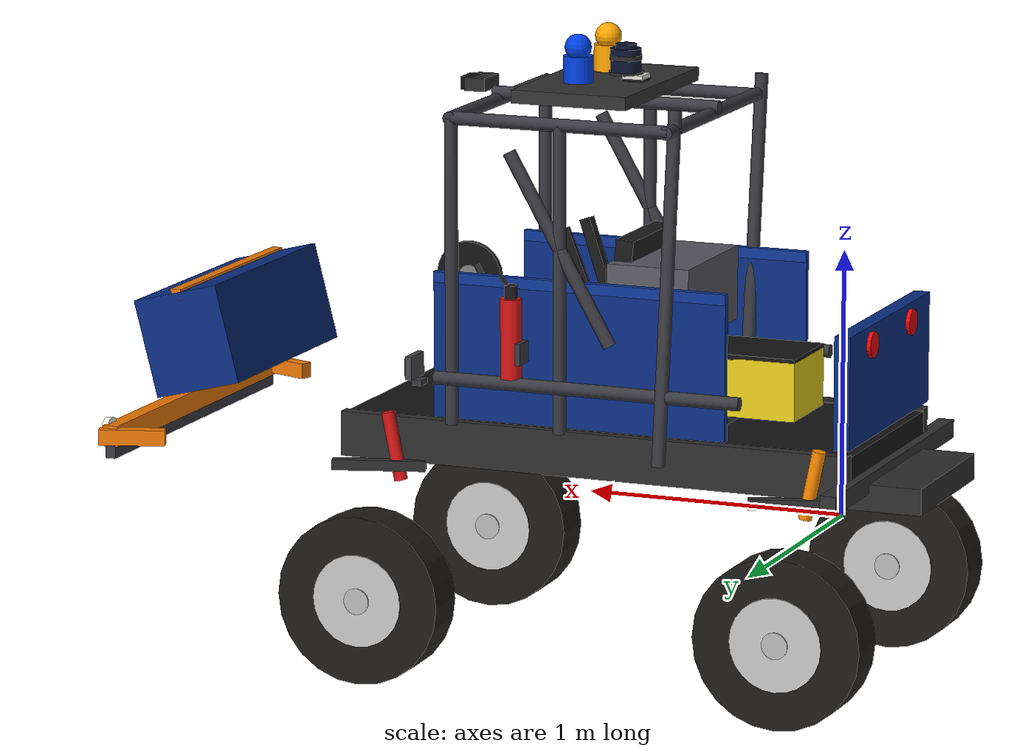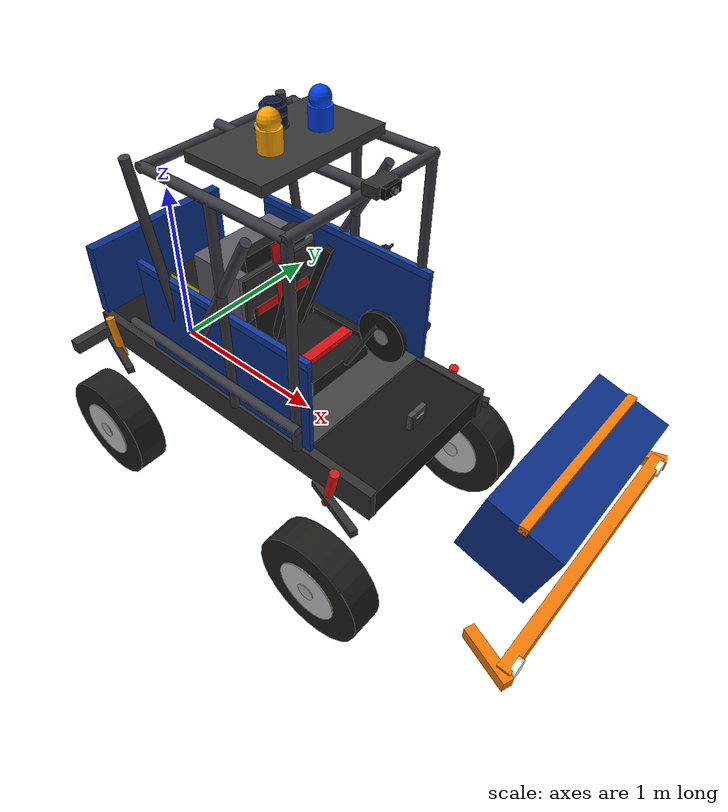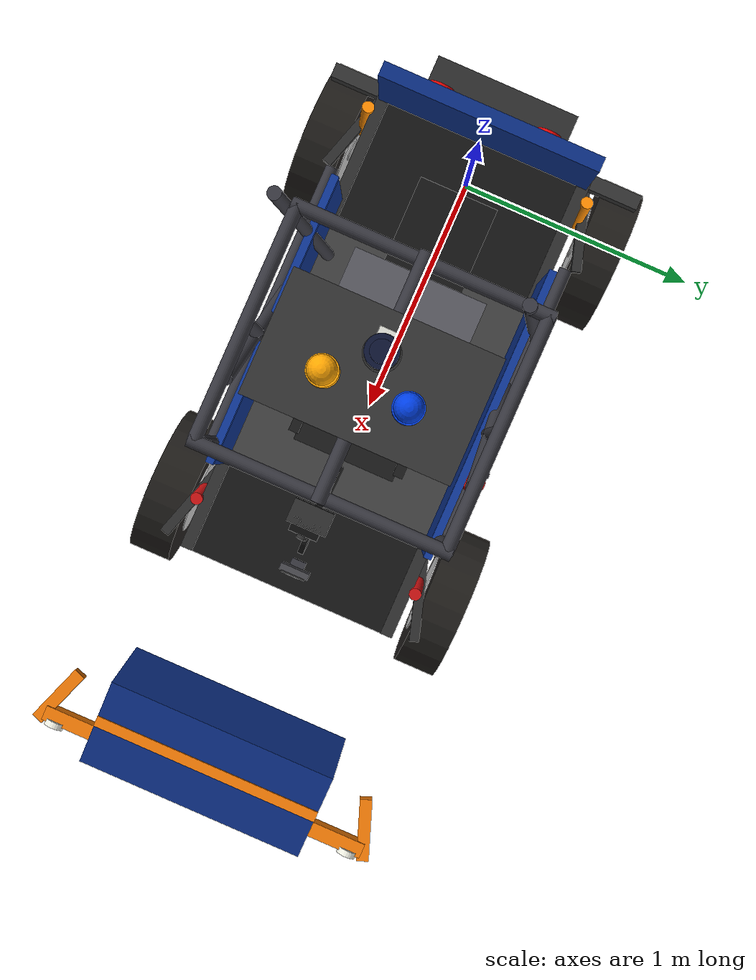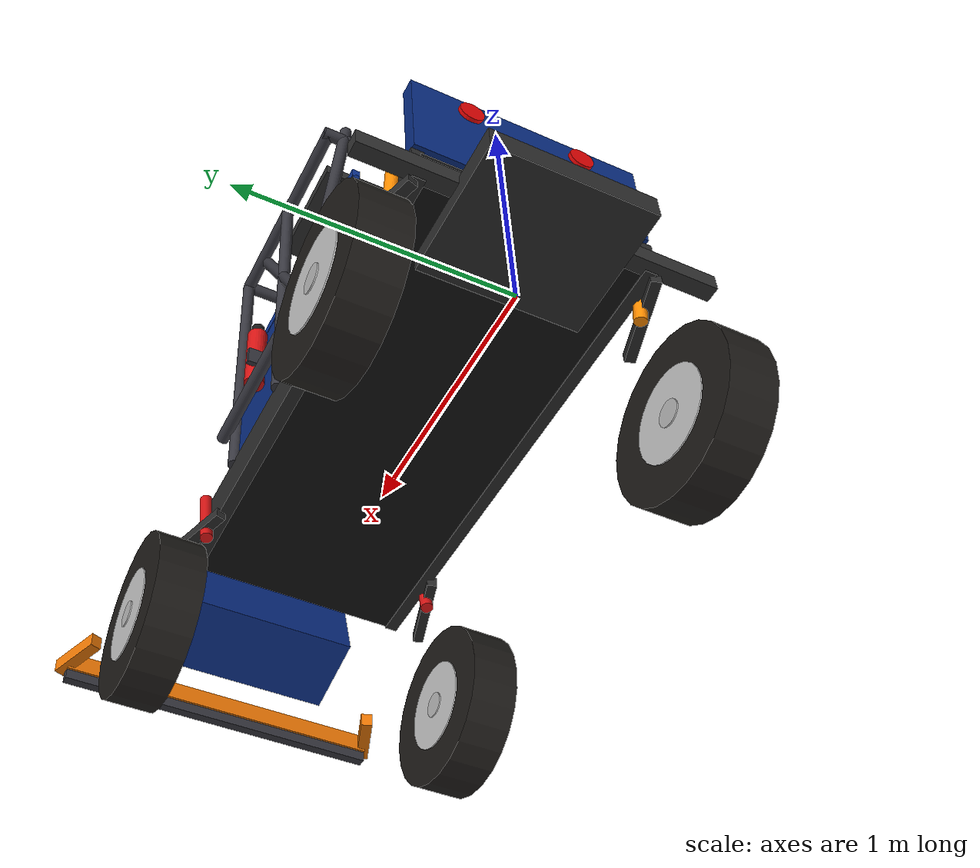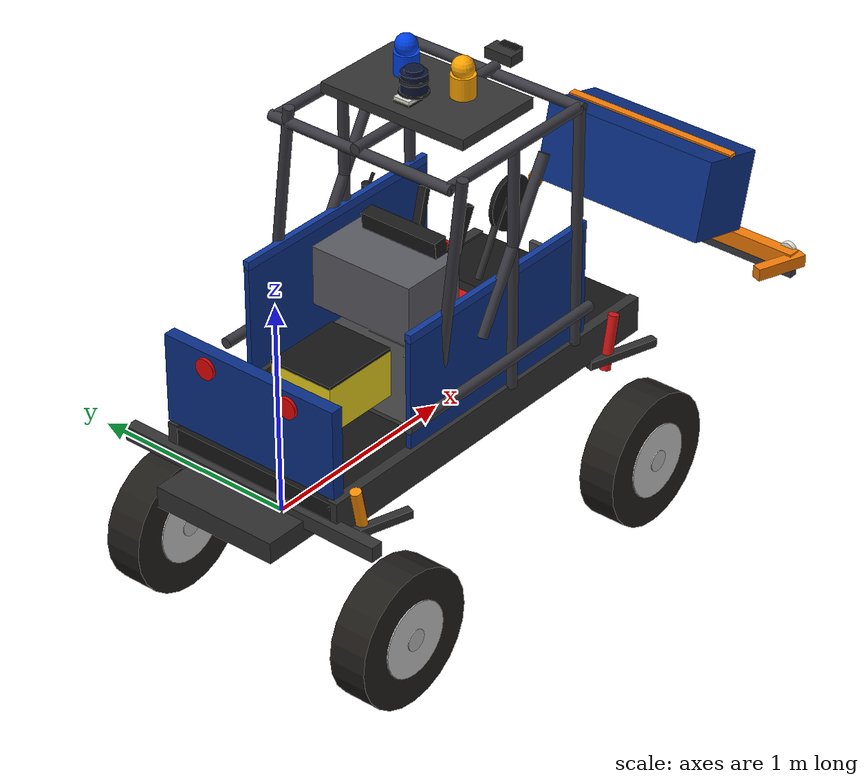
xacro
<?xml version="1.0"?>
<robot xmlns:xacro="http://www.ros.org/wiki/xacro" name="abaja_buggy">

  <!-- Color/material definitions (must be first) -->
  <xacro:include filename="$(find abaja_description)/urdf/materials.xacro"/>

  <!-- Chassis, roll cage, body, seat, beacons, electronics -->
  <xacro:include filename="$(find abaja_description)/urdf/chassis.xacro"/>

  <!-- Four wheels with steering and drive joints -->
  <xacro:include filename="$(find abaja_description)/urdf/wheels.xacro"/>

  <!-- Sensor mounts: camera, lidar, imu -->
  <xacro:include filename="$(find abaja_description)/urdf/sensors.xacro"/>

  <!-- Chassis -->
  <gazebo reference="chassis_link">
  </gazebo>

  <!-- Floor pan -->
  <gazebo reference="floor_pan_link">
  </gazebo>

  <!-- Body panels -->
  <gazebo reference="left_body_panel_link">
  </gazebo>
  <gazebo reference="right_body_panel_link">
  </gazebo>

  <!-- Roll cage elements -->
  <gazebo reference="roll_cage_front_hoop">
  </gazebo>
  <gazebo reference="roll_cage_rear_hoop">
  </gazebo>
  <gazebo reference="roll_cage_top_bar">
  </gazebo>
  <gazebo reference="roll_cage_left_pillar">
  </gazebo>
  <gazebo reference="roll_cage_right_pillar">
  </gazebo>
  <gazebo reference="roll_cage_left_rear_pillar">
  </gazebo>
  <gazebo reference="roll_cage_right_rear_pillar">
  </gazebo>
  <gazebo reference="roll_cage_left_side_bar">
  </gazebo>
  <gazebo reference="roll_cage_right_side_bar">
  </gazebo>

  <!-- Beacons -->
  <gazebo reference="asal_beacon_link">
  </gazebo>
  <gazebo reference="asal_beacon_dome">
  </gazebo>
  <gazebo reference="warning_beacon_link">
  </gazebo>
  <gazebo reference="warning_beacon_dome">
  </gazebo>

  <!-- Wheels -->
  <gazebo reference="front_left_wheel_link">
    <mu1>1.0</mu1>
    <mu2>1.0</mu2>
    <kp>1000000.0</kp>
    <kd>100.0</kd>
    <minDepth>0.001</minDepth>
  </gazebo>
  <gazebo reference="front_right_wheel_link">
    <mu1>1.0</mu1>
    <mu2>1.0</mu2>
    <kp>1000000.0</kp>
    <kd>100.0</kd>
    <minDepth>0.001</minDepth>
  </gazebo>
  <gazebo reference="rear_left_wheel_link">
    <mu1>1.0</mu1>
    <mu2>1.0</mu2>
    <kp>1000000.0</kp>
    <kd>100.0</kd>
    <minDepth>0.001</minDepth>
  </gazebo>
  <gazebo reference="rear_right_wheel_link">
    <mu1>1.0</mu1>
    <mu2>1.0</mu2>
    <kp>1000000.0</kp>
    <kd>100.0</kd>
    <minDepth>0.001</minDepth>
  </gazebo>

  <!-- Seat -->
  <gazebo reference="seat_link">
  </gazebo>
  <gazebo reference="seat_backrest_link">
  </gazebo>

  <!-- Battery and Electronics -->
  <gazebo reference="battery_box_link">
  </gazebo>
  <gazebo reference="electronics_box_link">
  </gazebo>

  <!-- Sensors -->
  <gazebo reference="camera_link">
  </gazebo>
  <gazebo reference="camera_mount_link">
  </gazebo>
  <!-- LiDAR — dark navy blue -->
  <gazebo reference="lidar_link">
  </gazebo>
  <!-- Starkenn Orion Radar — visual only, no Gazebo plugin -->
  <gazebo reference="radar_link">
  </gazebo>
  <!-- GPS — off-white patch antenna -->
  <gazebo reference="gps_link">
  </gazebo>
  <!-- IMU — green PCB -->
  <gazebo reference="imu_link">
  </gazebo>

  <!-- Hardware modules (visual-only, no Gazebo simulation plugins) -->
  <!-- Kvaser CAN network module -->
  <gazebo reference="kvaser_can_link">
  </gazebo>
  <!-- ESP32-C6 module — green PCB -->
  <gazebo reference="esp32_c6_link">
  </gazebo>
  <!-- SN65HVD230 CAN transceiver — blue-green -->
  <gazebo reference="sn65hvd230_link">
  </gazebo>

  <!-- Safety equipment -->
  <!-- Fire extinguisher — red -->
  <gazebo reference="fire_extinguisher_link">
  </gazebo>
  <!-- Harness straps — dark grey/black -->
  <gazebo reference="harness_left_strap">
  </gazebo>
  <gazebo reference="harness_right_strap">
  </gazebo>
  <gazebo reference="harness_lap_belt">
  </gazebo>

  <!-- Suspension springs -->
  <gazebo reference="front_left_spring">
  </gazebo>
  <gazebo reference="front_right_spring">
  </gazebo>
  <gazebo reference="rear_left_spring">
  </gazebo>
  <gazebo reference="rear_right_spring">
  </gazebo>

  <!-- New visual elements - bumpers, nose, guard -->
  <gazebo reference="front_nose_link">
  </gazebo>
  <gazebo reference="rear_guard_link">
  </gazebo>
  <gazebo reference="front_bumper_link">
  </gazebo>
  <gazebo reference="rear_bumper_link">
  </gazebo>
  <gazebo reference="front_left_light_link">
  </gazebo>
  <gazebo reference="front_right_light_link">
  </gazebo>
  <gazebo reference="left_tail_light">
  </gazebo>
  <gazebo reference="right_tail_light">
  </gazebo>
  <gazebo reference="roll_cage_front_left_upright">
  </gazebo>
  <gazebo reference="roll_cage_front_right_upright">
  </gazebo>
  <gazebo reference="roll_cage_diag_left">
  </gazebo>
  <gazebo reference="roll_cage_diag_right">
  </gazebo>
  <gazebo reference="side_protection_left">
  </gazebo>
  <gazebo reference="side_protection_right">
  </gazebo>

  <!-- Tail lights -->
  <gazebo reference="left_tail_light">
  </gazebo>
  <gazebo reference="right_tail_light">
  </gazebo>

  <gazebo>
    <plugin filename="gz-sim-diff-drive-system"
            name="gz::sim::systems::DiffDrive">
      <left_joint>rear_left_wheel_joint</left_joint>
      <right_joint>rear_right_wheel_joint</right_joint>
      <wheel_separation>1.25</wheel_separation>
      <wheel_radius>0.32</wheel_radius>
      <max_linear_acceleration>2.0</max_linear_acceleration>
      <odom_publish_frequency>50</odom_publish_frequency>
      <topic>cmd_vel</topic>
      <odom_topic>odom</odom_topic>
      <frame_id>odom</frame_id>
      <child_frame_id>base_link</child_frame_id>
    </plugin>
  </gazebo>

  <gazebo>
    <plugin filename="gz-sim-joint-state-publisher-system"
            name="gz::sim::systems::JointStatePublisher">
      <joint_name>front_left_wheel_joint</joint_name>
      <joint_name>front_right_wheel_joint</joint_name>
      <joint_name>rear_left_wheel_joint</joint_name>
      <joint_name>rear_right_wheel_joint</joint_name>
      <joint_name>front_left_steering_joint</joint_name>
      <joint_name>front_right_steering_joint</joint_name>
    </plugin>
  </gazebo>

</robot>

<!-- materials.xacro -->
<robot xmlns:xacro="http://www.ros.org/wiki/xacro" name="abaja_materials">

  <!-- ======================================================================
    CHASSIS AND STRUCTURAL COLORS
  ====================================================================== -->
  <!-- Main chassis / frame - near black -->
  <material name="Black">
    <color rgba="0.08 0.08 0.08 1.0"/>
  </material>

  <!-- Dark grey for structural/subframe elements -->
  <material name="DarkGrey">
    <color rgba="0.18 0.18 0.18 1.0"/>
  </material>

  <!-- Medium grey for metallic parts -->
  <material name="Grey">
    <color rgba="0.5 0.5 0.5 1.0"/>
  </material>

  <!-- Light grey for wheel rims and hub centers -->
  <material name="LightGrey">
    <color rgba="0.72 0.72 0.72 1.0"/>
  </material>

  <!-- ======================================================================
    ROLL CAGE AND FRAME
  ====================================================================== -->
  <!-- Roll cage - dark steel tube look -->
  <material name="Steel">
    <color rgba="0.22 0.22 0.25 1.0"/>
  </material>

  <!-- ======================================================================
    BODY PANEL COLORS - Team distinctive color
  ====================================================================== -->
  <!-- Side body panels: deep blue (team color, easily visible) -->
  <material name="BodyPanel">
    <color rgba="0.04 0.18 0.52 1.0"/>
  </material>

  <!-- Floor pan - dark grey -->
  <material name="FloorGrey">
    <color rgba="0.25 0.25 0.25 1.0"/>
  </material>

  <!-- Front nose panel - slightly lighter blue for differentiation -->
  <material name="FrontNose">
    <color rgba="0.06 0.22 0.60 1.0"/>
  </material>

  <!-- Rear guard / rear bumper panel -->
  <material name="RearGuard">
    <color rgba="0.04 0.18 0.52 1.0"/>
  </material>

  <!-- ======================================================================
    BUMPERS
  ====================================================================== -->
  <!-- Front bumper - safety orange accent for clear front identification -->
  <material name="BumperOrange">
    <color rgba="0.95 0.48 0.02 1.0"/>
  </material>

  <!-- Rear bumper - dark structural steel -->
  <material name="BumperGrey">
    <color rgba="0.20 0.20 0.20 1.0"/>
  </material>

  <!-- ======================================================================
    WHEEL AND TIRE COLORS
  ====================================================================== -->
  <!-- Tire rubber - near black with slight brown for realism -->
  <material name="TireBlack">
    <color rgba="0.12 0.11 0.10 1.0"/>
  </material>

  <!-- Wheel rim - silver/aluminium -->
  <material name="WheelRim">
    <color rgba="0.78 0.78 0.78 1.0"/>
  </material>

  <!-- ======================================================================
    SUSPENSION COLORS
  ====================================================================== -->
  <!-- Front spring/shock - Red (visible in real buggy) -->
  <material name="Red">
    <color rgba="0.85 0.08 0.08 1.0"/>
  </material>

  <!-- Rear spring/shock - Orange -->
  <material name="Orange">
    <color rgba="1.0 0.55 0.0 1.0"/>
  </material>

  <!-- ======================================================================
    BEACON AND LIGHT COLORS
  ====================================================================== -->
  <!-- Blue ASAL autonomous beacon -->
  <material name="Blue">
    <color rgba="0.0 0.25 0.9 1.0"/>
  </material>

  <!-- Amber warning beacon -->
  <material name="Amber">
    <color rgba="1.0 0.65 0.0 0.9"/>
  </material>

  <!-- Tail lights - bright red -->
  <material name="TailRed">
    <color rgba="0.9 0.02 0.02 1.0"/>
  </material>

  <!-- Front indicator lights - white -->
  <material name="FrontLight">
    <color rgba="0.95 0.95 0.90 1.0"/>
  </material>

  <!-- ======================================================================
    SENSOR COLORS
  ====================================================================== -->
  <!-- Camera housing - near black -->
  <material name="CameraBlack">
    <color rgba="0.05 0.05 0.05 1.0"/>
  </material>

  <!-- LiDAR - dark navy/blue-black -->
  <material name="LidarBlue">
    <color rgba="0.05 0.08 0.20 1.0"/>
  </material>

  <!-- Radar - dark grey -->
  <material name="RadarGrey">
    <color rgba="0.28 0.28 0.30 1.0"/>
  </material>

  <!-- Sensor mount bar - dark grey -->
  <material name="SensorBar">
    <color rgba="0.20 0.20 0.20 1.0"/>
  </material>

  <!-- ======================================================================
    ELECTRONICS AND BATTERY
  ====================================================================== -->
  <!-- Electronics box - medium grey -->
  <material name="ElectronicsGrey">
    <color rgba="0.35 0.35 0.38 1.0"/>
  </material>

  <!-- Battery box - safety yellow -->
  <material name="BatteryYellow">
    <color rgba="0.92 0.82 0.10 1.0"/>
  </material>

  <!-- ======================================================================
    SEAT AND COCKPIT
  ====================================================================== -->
  <!-- Seat - near black -->
  <material name="SeatBlack">
    <color rgba="0.10 0.10 0.10 1.0"/>
  </material>

  <!-- Seat harness stripe - red -->
  <material name="SeatRed">
    <color rgba="0.85 0.05 0.08 1.0"/>
  </material>

  <!-- Steering wheel -->
  <material name="SteeringBlack">
    <color rgba="0.08 0.08 0.08 1.0"/>
  </material>

  <!-- ESP32-C6 module — green PCB colour -->
  <material name="PCBGreen">
    <color rgba="0.13 0.55 0.13 1.0"/>
  </material>

  <!-- SN65HVD230 CAN transceiver — blue/green PCB -->
  <material name="PCBBlue">
    <color rgba="0.05 0.35 0.60 1.0"/>
  </material>

  <!-- Kvaser CAN network module — dark charcoal/black -->
  <material name="CANModule">
    <color rgba="0.15 0.15 0.16 1.0"/>
  </material>

  <!-- GPS antenna/receiver — off-white/light grey -->
  <material name="GPSWhite">
    <color rgba="0.88 0.88 0.85 1.0"/>
  </material>

  <!-- IMU sensor body — light olive green -->
  <material name="IMUGreen">
    <color rgba="0.30 0.50 0.20 1.0"/>
  </material>

  <!-- ======================================================================
    SAFETY EQUIPMENT
  ====================================================================== -->

  <!-- Fire extinguisher body — safety red -->
  <material name="FireExtRed">
    <color rgba="0.85 0.08 0.08 1.0"/>
  </material>

  <!-- Fire extinguisher head/nozzle — black -->
  <material name="FireExtHead">
    <color rgba="0.10 0.10 0.10 1.0"/>
  </material>

</robot>

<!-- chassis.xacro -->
<robot xmlns:xacro="http://www.ros.org/wiki/xacro" name="abaja_chassis">

  <!-- ======================================================================
    XACRO PROPERTIES
  ====================================================================== -->
  <xacro:property name="chassis_length" value="2.0"/>
  <xacro:property name="chassis_width"  value="0.85"/>
  <xacro:property name="chassis_height" value="0.15"/>
  <xacro:property name="chassis_mass"   value="80.0"/>
  <xacro:property name="ground_clearance" value="0.25"/>

  <xacro:property name="wheelbase"   value="1.65"/>
  <xacro:property name="track_width" value="1.25"/>

  <!-- Roll cage -->
  <xacro:property name="cage_tube_radius" value="0.025"/>
  <xacro:property name="cage_height"      value="1.15"/>

  <!-- Cockpit offset -->
  <xacro:property name="cockpit_offset_x" value="0.1"/>

  <!-- ======================================================================
    INERTIA MACROS
  ====================================================================== -->
  <xacro:macro name="box_inertia" params="mass x_dim y_dim z_dim">
    <inertial>
      <mass value="${mass}"/>
      <origin xyz="0 0 0" rpy="0 0 0"/>
      <inertia
        ixx="${(1.0/12.0) * mass * (y_dim*y_dim + z_dim*z_dim)}"
        ixy="0.0" ixz="0.0"
        iyy="${(1.0/12.0) * mass * (x_dim*x_dim + z_dim*z_dim)}"
        iyz="0.0"
        izz="${(1.0/12.0) * mass * (x_dim*x_dim + y_dim*y_dim)}"/>
    </inertial>
  </xacro:macro>

  <xacro:macro name="cylinder_inertia" params="mass radius length">
    <inertial>
      <mass value="${mass}"/>
      <origin xyz="0 0 0" rpy="0 0 0"/>
      <inertia
        ixx="${(1.0/12.0) * mass * (3*radius*radius + length*length)}"
        ixy="0.0" ixz="0.0"
        iyy="${(1.0/12.0) * mass * (3*radius*radius + length*length)}"
        iyz="0.0"
        izz="${(1.0/2.0) * mass * radius * radius}"/>
    </inertial>
  </xacro:macro>

  <xacro:macro name="sphere_inertia" params="mass radius">
    <inertial>
      <mass value="${mass}"/>
      <origin xyz="0 0 0" rpy="0 0 0"/>
      <inertia
        ixx="${(2.0/5.0) * mass * radius * radius}"
        ixy="0.0" ixz="0.0"
        iyy="${(2.0/5.0) * mass * radius * radius}"
        iyz="0.0"
        izz="${(2.0/5.0) * mass * radius * radius}"/>
    </inertial>
  </xacro:macro>

  <xacro:macro name="cage_tube" params="link_name tube_len tube_mass parent_link jnt_x jnt_y jnt_z jnt_r jnt_p jnt_yaw vis_r vis_p vis_yaw">
    <link name="${link_name}">
      <visual>
        <origin xyz="0 0 0" rpy="${vis_r} ${vis_p} ${vis_yaw}"/>
        <geometry><cylinder radius="${cage_tube_radius}" length="${tube_len}"/></geometry>
        <material name="Steel"/>
      </visual>
      <collision>
        <origin xyz="0 0 0" rpy="${vis_r} ${vis_p} ${vis_yaw}"/>
        <geometry><cylinder radius="${cage_tube_radius}" length="${tube_len}"/></geometry>
      </collision>
      <xacro:cylinder_inertia mass="${tube_mass}" radius="${cage_tube_radius}" length="${tube_len}"/>
    </link>
    <joint name="${link_name}_joint" type="fixed">
      <parent link="${parent_link}"/>
      <child  link="${link_name}"/>
      <origin xyz="${jnt_x} ${jnt_y} ${jnt_z}" rpy="${jnt_r} ${jnt_p} ${jnt_yaw}"/>
    </joint>
  </xacro:macro>

  <link name="dummy_root">
    <!-- Massless root link (KDL requirement) -->
  </link>

  <joint name="dummy_to_base" type="fixed">
    <parent link="dummy_root"/>
    <child  link="base_link"/>
    <origin xyz="0 0 0" rpy="0 0 0"/>
  </joint>

  <link name="base_link">
    <inertial>
      <mass value="0.001"/>
      <origin xyz="0 0 0" rpy="0 0 0"/>
      <inertia ixx="0.001" ixy="0" ixz="0" iyy="0.001" iyz="0" izz="0.001"/>
    </inertial>
  </link>

  <link name="base_footprint">
    <inertial>
      <mass value="0.001"/>
      <origin xyz="0 0 0" rpy="0 0 0"/>
      <inertia ixx="0.001" ixy="0" ixz="0" iyy="0.001" iyz="0" izz="0.001"/>
    </inertial>
  </link>

  <joint name="base_footprint_joint" type="fixed">
    <parent link="base_link"/>
    <child  link="base_footprint"/>
    <origin xyz="0 0 0" rpy="0 0 0"/>
  </joint>

  <link name="chassis_link">
    <!-- Main lower chassis tube frame (longitudinal rail) -->
    <visual>
      <origin xyz="${wheelbase/2} 0 0" rpy="0 0 0"/>
      <geometry><box size="${chassis_length} ${chassis_width} ${chassis_height}"/></geometry>
      <material name="Black"/>
    </visual>
    <!-- Left chassis rail (visual highlight) -->
    <visual>
      <origin xyz="${wheelbase/2} ${chassis_width/2 + 0.01} 0" rpy="0 0 0"/>
      <geometry><box size="${chassis_length} 0.05 ${chassis_height + 0.02}"/></geometry>
      <material name="DarkGrey"/>
    </visual>
    <!-- Right chassis rail -->
    <visual>
      <origin xyz="${wheelbase/2} -${chassis_width/2 + 0.01} 0" rpy="0 0 0"/>
      <geometry><box size="${chassis_length} 0.05 ${chassis_height + 0.02}"/></geometry>
      <material name="DarkGrey"/>
    </visual>
    <collision>
      <origin xyz="${wheelbase/2} 0 0" rpy="0 0 0"/>
      <geometry><box size="${chassis_length} ${chassis_width} ${chassis_height}"/></geometry>
    </collision>
    <xacro:box_inertia mass="${chassis_mass}" x_dim="${chassis_length}" y_dim="${chassis_width}" z_dim="${chassis_height}"/>
  </link>

  <joint name="base_to_chassis" type="fixed">
    <parent link="base_link"/>
    <child  link="chassis_link"/>
    <origin xyz="0 0 ${ground_clearance}" rpy="0 0 0"/>
  </joint>

  <!-- ======================================================================
    FLOOR PAN (preserved)
  ====================================================================== -->
  <link name="floor_pan_link">
    <visual>
      <origin xyz="0 0 0" rpy="0 0 0"/>
      <geometry><box size="1.0 ${chassis_width} 0.02"/></geometry>
      <material name="FloorGrey"/>
    </visual>
    <collision>
      <origin xyz="0 0 0" rpy="0 0 0"/>
      <geometry><box size="1.0 ${chassis_width} 0.02"/></geometry>
    </collision>
    <xacro:box_inertia mass="8.0" x_dim="1.0" y_dim="${chassis_width}" z_dim="0.02"/>
  </link>

  <joint name="chassis_to_floor" type="fixed">
    <parent link="chassis_link"/>
    <child  link="floor_pan_link"/>
    <origin xyz="${wheelbase/2 + 0.1} 0 ${chassis_height/2 + 0.01}" rpy="0 0 0"/>
  </joint>

  <!-- Left body panel - full cockpit height, team blue -->
  <link name="left_body_panel_link">
    <visual>
      <origin xyz="0 0 0" rpy="0 0 0"/>
      <geometry><box size="1.15 0.025 0.52"/></geometry>
      <material name="BodyPanel"/>
    </visual>
    <!-- Panel stripe accent (lighter blue strip along top) -->
    <visual>
      <origin xyz="0 0 0.27" rpy="0 0 0"/>
      <geometry><box size="1.15 0.03 0.04"/></geometry>
      <material name="FrontNose"/>
    </visual>
    <collision>
      <origin xyz="0 0 0" rpy="0 0 0"/>
      <geometry><box size="1.15 0.025 0.52"/></geometry>
    </collision>
    <xacro:box_inertia mass="3.5" x_dim="1.15" y_dim="0.025" z_dim="0.52"/>
  </link>

  <joint name="chassis_to_left_panel" type="fixed">
    <parent link="chassis_link"/>
    <child  link="left_body_panel_link"/>
    <origin xyz="${wheelbase/2 + 0.05} ${chassis_width/2 + 0.01} ${chassis_height/2 + 0.28}" rpy="0 0 0"/>
  </joint>

  <!-- Right body panel -->
  <link name="right_body_panel_link">
    <visual>
      <origin xyz="0 0 0" rpy="0 0 0"/>
      <geometry><box size="1.15 0.025 0.52"/></geometry>
      <material name="BodyPanel"/>
    </visual>
    <visual>
      <origin xyz="0 0 0.27" rpy="0 0 0"/>
      <geometry><box size="1.15 0.03 0.04"/></geometry>
      <material name="FrontNose"/>
    </visual>
    <collision>
      <origin xyz="0 0 0" rpy="0 0 0"/>
      <geometry><box size="1.15 0.025 0.52"/></geometry>
    </collision>
    <xacro:box_inertia mass="3.5" x_dim="1.15" y_dim="0.025" z_dim="0.52"/>
  </link>

  <joint name="chassis_to_right_panel" type="fixed">
    <parent link="chassis_link"/>
    <child  link="right_body_panel_link"/>
    <origin xyz="${wheelbase/2 + 0.05} -${chassis_width/2 + 0.01} ${chassis_height/2 + 0.28}" rpy="0 0 0"/>
  </joint>

  <link name="front_nose_link">
    <!-- Main angled nose plate -->
    <visual>
      <origin xyz="0 0 0" rpy="0 0.25 0"/>
      <geometry><box size="0.35 ${chassis_width + 0.05} 0.38"/></geometry>
      <material name="BodyPanel"/>
    </visual>
    <!-- Nose accent stripe (orange) -->
    <visual>
      <origin xyz="0.04 0 0.18" rpy="0 0 0"/>
      <geometry><box size="0.04 ${chassis_width + 0.05} 0.04"/></geometry>
      <material name="BumperOrange"/>
    </visual>
    <collision>
      <origin xyz="0 0 0" rpy="0 0.25 0"/>
      <geometry><box size="0.35 ${chassis_width + 0.05} 0.38"/></geometry>
    </collision>
    <xacro:box_inertia mass="2.0" x_dim="0.35" y_dim="${chassis_width + 0.05}" z_dim="0.38"/>
  </link>

  <joint name="chassis_to_front_nose" type="fixed">
    <parent link="chassis_link"/>
    <child  link="front_nose_link"/>
    <origin xyz="${wheelbase + 0.82} 0 ${chassis_height/2 + 0.22}" rpy="0 0 0"/>
  </joint>

  <!-- ======================================================================
    REAR BODY PANEL / REAR GUARD
  ====================================================================== -->
  <link name="rear_guard_link">
    <visual>
      <origin xyz="0 0 0" rpy="0 0 0"/>
      <geometry><box size="0.06 ${chassis_width + 0.05} 0.42"/></geometry>
      <material name="RearGuard"/>
    </visual>
    <collision>
      <origin xyz="0 0 0" rpy="0 0 0"/>
      <geometry><box size="0.06 ${chassis_width + 0.05} 0.42"/></geometry>
    </collision>
    <xacro:box_inertia mass="2.0" x_dim="0.06" y_dim="${chassis_width + 0.05}" z_dim="0.42"/>
  </link>

  <joint name="chassis_to_rear_guard" type="fixed">
    <parent link="chassis_link"/>
    <child  link="rear_guard_link"/>
    <origin xyz="-0.15 0 ${chassis_height/2 + 0.24}" rpy="0 0 0"/>
  </joint>

  <link name="front_bumper_link">
    <!-- Main bumper bar -->
    <visual>
      <origin xyz="0 0 0" rpy="0 0 0"/>
      <geometry><box size="0.06 ${track_width + 0.15} 0.08"/></geometry>
      <material name="BumperOrange"/>
    </visual>
    <!-- Left bumper horn -->
    <visual>
      <origin xyz="-0.08 ${track_width/2 + 0.05} 0" rpy="0 0 0.35"/>
      <geometry><box size="0.25 0.05 0.06"/></geometry>
      <material name="BumperOrange"/>
    </visual>
    <!-- Right bumper horn -->
    <visual>
      <origin xyz="-0.08 -${track_width/2 + 0.05} 0" rpy="0 0 -0.35"/>
      <geometry><box size="0.25 0.05 0.06"/></geometry>
      <material name="BumperOrange"/>
    </visual>
    <!-- Bumper skid plate (lower) -->
    <visual>
      <origin xyz="0 0 -0.06" rpy="0 0 0"/>
      <geometry><box size="0.04 ${track_width + 0.15} 0.05"/></geometry>
      <material name="Steel"/>
    </visual>
    <collision>
      <origin xyz="0 0 0" rpy="0 0 0"/>
      <geometry><box size="0.08 ${track_width + 0.15} 0.08"/></geometry>
    </collision>
    <xacro:box_inertia mass="3.0" x_dim="0.08" y_dim="${track_width + 0.15}" z_dim="0.08"/>
  </link>

  <joint name="chassis_to_front_bumper" type="fixed">
    <parent link="chassis_link"/>
    <child  link="front_bumper_link"/>
    <origin xyz="${wheelbase + 1.02} 0 ${-chassis_height/2 + 0.04}" rpy="0 0 0"/>
  </joint>

  <!-- Front indicator lights (white, mounted on bumper corners) -->
  <link name="front_left_light_link">
    <visual>
      <origin xyz="0 0 0" rpy="0 1.5708 0"/>
      <geometry><cylinder radius="0.04" length="0.025"/></geometry>
      <material name="FrontLight"/>
    </visual>
    <collision>
      <origin xyz="0 0 0" rpy="0 1.5708 0"/>
      <geometry><cylinder radius="0.04" length="0.025"/></geometry>
    </collision>
    <xacro:cylinder_inertia mass="0.05" radius="0.04" length="0.025"/>
  </link>

  <joint name="bumper_to_fl_light" type="fixed">
    <parent link="front_bumper_link"/>
    <child  link="front_left_light_link"/>
    <origin xyz="0.03 ${track_width/2 + 0.02} 0.02" rpy="0 0 0"/>
  </joint>

  <link name="front_right_light_link">
    <visual>
      <origin xyz="0 0 0" rpy="0 1.5708 0"/>
      <geometry><cylinder radius="0.04" length="0.025"/></geometry>
      <material name="FrontLight"/>
    </visual>
    <collision>
      <origin xyz="0 0 0" rpy="0 1.5708 0"/>
      <geometry><cylinder radius="0.04" length="0.025"/></geometry>
    </collision>
    <xacro:cylinder_inertia mass="0.05" radius="0.04" length="0.025"/>
  </link>

  <joint name="bumper_to_fr_light" type="fixed">
    <parent link="front_bumper_link"/>
    <child  link="front_right_light_link"/>
    <origin xyz="0.03 -${track_width/2 + 0.02} 0.02" rpy="0 0 0"/>
  </joint>

  <!-- ======================================================================
    REAR BUMPER
  ====================================================================== -->
  <link name="rear_bumper_link">
    <!-- Main rear bumper bar -->
    <visual>
      <origin xyz="0 0 0" rpy="0 0 0"/>
      <geometry><box size="0.06 ${track_width + 0.1} 0.07"/></geometry>
      <material name="BumperGrey"/>
    </visual>
    <!-- Rear tow hook visual -->
    <visual>
      <origin xyz="-0.05 0 -0.04" rpy="0 0 0"/>
      <geometry><box size="0.08 0.04 0.04"/></geometry>
      <material name="Steel"/>
    </visual>
    <collision>
      <origin xyz="0 0 0" rpy="0 0 0"/>
      <geometry><box size="0.06 ${track_width + 0.1} 0.07"/></geometry>
    </collision>
    <xacro:box_inertia mass="2.5" x_dim="0.06" y_dim="${track_width + 0.1}" z_dim="0.07"/>
  </link>

  <joint name="chassis_to_rear_bumper" type="fixed">
    <parent link="chassis_link"/>
    <child  link="rear_bumper_link"/>
    <origin xyz="-0.18 0 ${-chassis_height/2 + 0.03}" rpy="0 0 0"/>
  </joint>

  <!-- ── FRONT HOOP ─────────────────────────────────────────── -->
  <!-- Front hoop: left pillar (cylinder, vertical) -->
  <xacro:cage_tube
    link_name="roll_cage_front_left_upright"
    tube_len="${cage_height}"
    tube_mass="2.0"
    parent_link="chassis_link"
    jnt_x="${wheelbase/2 + 0.55}" jnt_y="${chassis_width/2 + 0.03}" jnt_z="${chassis_height/2 + cage_height/2}"
    jnt_r="0" jnt_p="0" jnt_yaw="0"
    vis_r="0" vis_p="0" vis_yaw="0"/>

  <!-- Front hoop: right pillar -->
  <xacro:cage_tube
    link_name="roll_cage_front_right_upright"
    tube_len="${cage_height}"
    tube_mass="2.0"
    parent_link="chassis_link"
    jnt_x="${wheelbase/2 + 0.55}" jnt_y="-${chassis_width/2 + 0.03}" jnt_z="${chassis_height/2 + cage_height/2}"
    jnt_r="0" jnt_p="0" jnt_yaw="0"
    vis_r="0" vis_p="0" vis_yaw="0"/>

  <!-- Front hoop: top cross tube (horizontal, Y direction) -->
  <link name="roll_cage_front_hoop">
    <visual>
      <origin xyz="0 0 0" rpy="${pi/2} 0 0"/>
      <geometry><cylinder radius="${cage_tube_radius}" length="${chassis_width + 0.1}"/></geometry>
      <material name="Steel"/>
    </visual>
    <collision>
      <origin xyz="0 0 0" rpy="${pi/2} 0 0"/>
      <geometry><cylinder radius="${cage_tube_radius}" length="${chassis_width + 0.1}"/></geometry>
    </collision>
    <xacro:cylinder_inertia mass="1.5" radius="${cage_tube_radius}" length="${chassis_width + 0.1}"/>
  </link>
  <joint name="chassis_to_front_hoop" type="fixed">
    <parent link="chassis_link"/>
    <child  link="roll_cage_front_hoop"/>
    <origin xyz="${wheelbase/2 + 0.55} 0 ${chassis_height/2 + cage_height}" rpy="0 0 0"/>
  </joint>

  <!-- ── REAR HOOP ──────────────────────────────────────────── -->
  <!-- Rear hoop: left upright (with slight outward lean for BAJA style) -->
  <link name="roll_cage_left_rear_pillar">
    <visual>
      <origin xyz="0 0 0" rpy="0.12 0 0"/>
      <geometry><cylinder radius="${cage_tube_radius}" length="${cage_height + 0.15}"/></geometry>
      <material name="Steel"/>
    </visual>
    <collision>
      <origin xyz="0 0 0" rpy="0.12 0 0"/>
      <geometry><cylinder radius="${cage_tube_radius}" length="${cage_height + 0.15}"/></geometry>
    </collision>
    <xacro:cylinder_inertia mass="2.5" radius="${cage_tube_radius}" length="${cage_height + 0.15}"/>
  </link>
  <joint name="chassis_to_left_rear_pillar" type="fixed">
    <parent link="chassis_link"/>
    <child  link="roll_cage_left_rear_pillar"/>
    <origin xyz="${wheelbase/2 - 0.30} ${chassis_width/2 + 0.03} ${chassis_height/2 + cage_height/2}" rpy="0 0 0"/>
  </joint>

  <!-- Rear hoop: right upright -->
  <link name="roll_cage_right_rear_pillar">
    <visual>
      <origin xyz="0 0 0" rpy="0.12 0 0"/>
      <geometry><cylinder radius="${cage_tube_radius}" length="${cage_height + 0.15}"/></geometry>
      <material name="Steel"/>
    </visual>
    <collision>
      <origin xyz="0 0 0" rpy="0.12 0 0"/>
      <geometry><cylinder radius="${cage_tube_radius}" length="${cage_height + 0.15}"/></geometry>
    </collision>
    <xacro:cylinder_inertia mass="2.5" radius="${cage_tube_radius}" length="${cage_height + 0.15}"/>
  </link>
  <joint name="chassis_to_right_rear_pillar" type="fixed">
    <parent link="chassis_link"/>
    <child  link="roll_cage_right_rear_pillar"/>
    <origin xyz="${wheelbase/2 - 0.30} -${chassis_width/2 + 0.03} ${chassis_height/2 + cage_height/2}" rpy="0 0 0"/>
  </joint>

  <!-- Rear hoop: top cross bar -->
  <link name="roll_cage_rear_hoop">
    <visual>
      <origin xyz="0 0 0" rpy="${pi/2} 0 0"/>
      <geometry><cylinder radius="${cage_tube_radius}" length="${chassis_width + 0.1}"/></geometry>
      <material name="Steel"/>
    </visual>
    <collision>
      <origin xyz="0 0 0" rpy="${pi/2} 0 0"/>
      <geometry><cylinder radius="${cage_tube_radius}" length="${chassis_width + 0.1}"/></geometry>
    </collision>
    <xacro:cylinder_inertia mass="1.5" radius="${cage_tube_radius}" length="${chassis_width + 0.1}"/>
  </link>
  <joint name="chassis_to_rear_hoop" type="fixed">
    <parent link="chassis_link"/>
    <child  link="roll_cage_rear_hoop"/>
    <origin xyz="${wheelbase/2 - 0.30} 0 ${chassis_height/2 + cage_height}" rpy="0 0 0"/>
  </joint>

  <!-- ── A-PILLAR (front cage uprights connecting front hoop to chassis sides) -->
  <!-- Preserved names from original for Gazebo/abaja_buggy.urdf.xacro compatibility -->
  <link name="roll_cage_left_pillar">
    <visual>
      <origin xyz="0 0 0" rpy="0 0 0"/>
      <geometry><cylinder radius="${cage_tube_radius}" length="${cage_height}"/></geometry>
      <material name="Steel"/>
    </visual>
    <collision>
      <origin xyz="0 0 0" rpy="0 0 0"/>
      <geometry><cylinder radius="${cage_tube_radius}" length="${cage_height}"/></geometry>
    </collision>
    <xacro:cylinder_inertia mass="2.0" radius="${cage_tube_radius}" length="${cage_height}"/>
  </link>
  <joint name="chassis_to_left_pillar" type="fixed">
    <parent link="chassis_link"/>
    <child  link="roll_cage_left_pillar"/>
    <origin xyz="${wheelbase/2 + 0.12} ${chassis_width/2 + 0.03} ${chassis_height/2 + cage_height/2}" rpy="0 0 0"/>
  </joint>

  <link name="roll_cage_right_pillar">
    <visual>
      <origin xyz="0 0 0" rpy="0 0 0"/>
      <geometry><cylinder radius="${cage_tube_radius}" length="${cage_height}"/></geometry>
      <material name="Steel"/>
    </visual>
    <collision>
      <origin xyz="0 0 0" rpy="0 0 0"/>
      <geometry><cylinder radius="${cage_tube_radius}" length="${cage_height}"/></geometry>
    </collision>
    <xacro:cylinder_inertia mass="2.0" radius="${cage_tube_radius}" length="${cage_height}"/>
  </link>
  <joint name="chassis_to_right_pillar" type="fixed">
    <parent link="chassis_link"/>
    <child  link="roll_cage_right_pillar"/>
    <origin xyz="${wheelbase/2 + 0.12} -${chassis_width/2 + 0.03} ${chassis_height/2 + cage_height/2}" rpy="0 0 0"/>
  </joint>

  <!-- ── TOP CONNECTING BAR (front hoop to rear hoop, left and right) ── -->
  <link name="roll_cage_top_bar">
    <visual>
      <origin xyz="0 0 0" rpy="0 ${pi/2} 0"/>
      <geometry><cylinder radius="${cage_tube_radius}" length="0.90"/></geometry>
      <material name="Steel"/>
    </visual>
    <collision>
      <origin xyz="0 0 0" rpy="0 ${pi/2} 0"/>
      <geometry><cylinder radius="${cage_tube_radius}" length="0.90"/></geometry>
    </collision>
    <xacro:cylinder_inertia mass="1.5" radius="${cage_tube_radius}" length="0.90"/>
  </link>
  <joint name="chassis_to_top_bar" type="fixed">
    <parent link="chassis_link"/>
    <child  link="roll_cage_top_bar"/>
    <origin xyz="${wheelbase/2 + 0.12} 0 ${chassis_height/2 + cage_height + 0.025}" rpy="0 0 0"/>
  </joint>

  <!-- Top left longtudinal bar -->
  <link name="roll_cage_left_side_bar">
    <visual>
      <origin xyz="0 0 0" rpy="0 ${pi/2} 0"/>
      <geometry><cylinder radius="${cage_tube_radius}" length="0.85"/></geometry>
      <material name="Steel"/>
    </visual>
    <collision>
      <origin xyz="0 0 0" rpy="0 ${pi/2} 0"/>
      <geometry><cylinder radius="${cage_tube_radius}" length="0.85"/></geometry>
    </collision>
    <xacro:cylinder_inertia mass="1.5" radius="${cage_tube_radius}" length="0.85"/>
  </link>
  <joint name="chassis_to_left_side_bar" type="fixed">
    <parent link="chassis_link"/>
    <child  link="roll_cage_left_side_bar"/>
    <origin xyz="${wheelbase/2 + 0.12} ${chassis_width/2 + 0.03} ${chassis_height/2 + cage_height}" rpy="0 0 0"/>
  </joint>

  <!-- Top right longitudinal bar -->
  <link name="roll_cage_right_side_bar">
    <visual>
      <origin xyz="0 0 0" rpy="0 ${pi/2} 0"/>
      <geometry><cylinder radius="${cage_tube_radius}" length="0.85"/></geometry>
      <material name="Steel"/>
    </visual>
    <collision>
      <origin xyz="0 0 0" rpy="0 ${pi/2} 0"/>
      <geometry><cylinder radius="${cage_tube_radius}" length="0.85"/></geometry>
    </collision>
    <xacro:cylinder_inertia mass="1.5" radius="${cage_tube_radius}" length="0.85"/>
  </link>
  <joint name="chassis_to_right_side_bar" type="fixed">
    <parent link="chassis_link"/>
    <child  link="roll_cage_right_side_bar"/>
    <origin xyz="${wheelbase/2 + 0.12} -${chassis_width/2 + 0.03} ${chassis_height/2 + cage_height}" rpy="0 0 0"/>
  </joint>

  <!-- ── DIAGONAL BRACES (X-brace pattern at rear of roll cage) ── -->
  <xacro:cage_tube
    link_name="roll_cage_diag_left"
    tube_len="0.80"
    tube_mass="1.0"
    parent_link="chassis_link"
    jnt_x="${wheelbase/2 + 0.12}" jnt_y="${chassis_width/2 + 0.03}" jnt_z="${chassis_height/2 + cage_height * 0.60}"
    jnt_r="0" jnt_p="0" jnt_yaw="0"
    vis_r="0" vis_p="0.52" vis_yaw="0"/>

  <xacro:cage_tube
    link_name="roll_cage_diag_right"
    tube_len="0.80"
    tube_mass="1.0"
    parent_link="chassis_link"
    jnt_x="${wheelbase/2 + 0.12}" jnt_y="-${chassis_width/2 + 0.03}" jnt_z="${chassis_height/2 + cage_height * 0.60}"
    jnt_r="0" jnt_p="0" jnt_yaw="0"
    vis_r="0" vis_p="0.52" vis_yaw="0"/>

  <!-- ── SIDE PROTECTION BARS (low horizontal tube along body sides) ── -->
  <xacro:cage_tube
    link_name="side_protection_left"
    tube_len="1.20"
    tube_mass="2.0"
    parent_link="chassis_link"
    jnt_x="${wheelbase/2}" jnt_y="${chassis_width/2 + 0.07}" jnt_z="${chassis_height/2 + 0.18}"
    jnt_r="0" jnt_p="0" jnt_yaw="0"
    vis_r="0" vis_p="${pi/2}" vis_yaw="0"/>

  <xacro:cage_tube
    link_name="side_protection_right"
    tube_len="1.20"
    tube_mass="2.0"
    parent_link="chassis_link"
    jnt_x="${wheelbase/2}" jnt_y="-${chassis_width/2 + 0.07}" jnt_z="${chassis_height/2 + 0.18}"
    jnt_r="0" jnt_p="0" jnt_yaw="0"
    vis_r="0" vis_p="${pi/2}" vis_yaw="0"/>

  <!-- ======================================================================
    SENSOR MOUNT BAR (preserved name/joint)
  ====================================================================== -->
  <link name="sensor_mount_bar">
    <visual>
      <origin xyz="0 0 0" rpy="0 0 0"/>
      <geometry><box size="0.45 0.75 0.05"/></geometry>
      <material name="SensorBar"/>
    </visual>
    <!-- Mounting rail left -->
    <visual>
      <origin xyz="0 0.30 0" rpy="0 0 0"/>
      <geometry><box size="0.42 0.04 0.03"/></geometry>
      <material name="DarkGrey"/>
    </visual>
    <!-- Mounting rail right -->
    <visual>
      <origin xyz="0 -0.30 0" rpy="0 0 0"/>
      <geometry><box size="0.42 0.04 0.03"/></geometry>
      <material name="DarkGrey"/>
    </visual>
    <collision>
      <origin xyz="0 0 0" rpy="0 0 0"/>
      <geometry><box size="0.45 0.75 0.05"/></geometry>
    </collision>
    <xacro:box_inertia mass="2.0" x_dim="0.45" y_dim="0.75" z_dim="0.05"/>
  </link>

  <joint name="cage_to_sensor_bar" type="fixed">
    <parent link="chassis_link"/>
    <child  link="sensor_mount_bar"/>
    <origin xyz="${wheelbase/2 + 0.12} 0 ${chassis_height/2 + cage_height + 0.08}" rpy="0 0 0"/>
  </joint>

  <!-- ======================================================================
    BEACONS (preserved names and joints)
  ====================================================================== -->
  <!-- Blue ASAL beacon -->
  <link name="asal_beacon_link">
    <visual>
      <origin xyz="0 0 0" rpy="0 0 0"/>
      <geometry><cylinder radius="0.055" length="0.10"/></geometry>
      <material name="Blue"/>
    </visual>
    <collision>
      <origin xyz="0 0 0" rpy="0 0 0"/>
      <geometry><cylinder radius="0.055" length="0.10"/></geometry>
    </collision>
    <xacro:cylinder_inertia mass="0.3" radius="0.055" length="0.10"/>
  </link>

  <link name="asal_beacon_dome">
    <visual>
      <origin xyz="0 0 0" rpy="0 0 0"/>
      <geometry><sphere radius="0.050"/></geometry>
      <material name="Blue"/>
    </visual>
    <collision>
      <origin xyz="0 0 0" rpy="0 0 0"/>
      <geometry><sphere radius="0.050"/></geometry>
    </collision>
    <xacro:sphere_inertia mass="0.1" radius="0.050"/>
  </link>

  <joint name="sensor_bar_to_asal_beacon" type="fixed">
    <parent link="sensor_mount_bar"/>
    <child  link="asal_beacon_link"/>
    <origin xyz="0.05 0.15 0.08" rpy="0 0 0"/>
  </joint>

  <joint name="asal_beacon_to_dome" type="fixed">
    <parent link="asal_beacon_link"/>
    <child  link="asal_beacon_dome"/>
    <origin xyz="0 0 0.08" rpy="0 0 0"/>
  </joint>

  <!-- Orange warning beacon -->
  <link name="warning_beacon_link">
    <visual>
      <origin xyz="0 0 0" rpy="0 0 0"/>
      <geometry><cylinder radius="0.055" length="0.10"/></geometry>
      <material name="Amber"/>
    </visual>
    <collision>
      <origin xyz="0 0 0" rpy="0 0 0"/>
      <geometry><cylinder radius="0.055" length="0.10"/></geometry>
    </collision>
    <xacro:cylinder_inertia mass="0.3" radius="0.055" length="0.10"/>
  </link>

  <link name="warning_beacon_dome">
    <visual>
      <origin xyz="0 0 0" rpy="0 0 0"/>
      <geometry><sphere radius="0.050"/></geometry>
      <material name="Amber"/>
    </visual>
    <collision>
      <origin xyz="0 0 0" rpy="0 0 0"/>
      <geometry><sphere radius="0.050"/></geometry>
    </collision>
    <xacro:sphere_inertia mass="0.1" radius="0.050"/>
  </link>

  <joint name="sensor_bar_to_warning_beacon" type="fixed">
    <parent link="sensor_mount_bar"/>
    <child  link="warning_beacon_link"/>
    <origin xyz="0.05 -0.15 0.08" rpy="0 0 0"/>
  </joint>

  <joint name="warning_beacon_to_dome" type="fixed">
    <parent link="warning_beacon_link"/>
    <child  link="warning_beacon_dome"/>
    <origin xyz="0 0 0.08" rpy="0 0 0"/>
  </joint>

  <!-- ======================================================================
    SEAT - Preserved names
  ====================================================================== -->
  <link name="seat_link">
    <!-- Seat base cushion -->
    <visual>
      <origin xyz="0 0 0" rpy="0 0 0"/>
      <geometry><box size="0.45 0.42 0.09"/></geometry>
      <material name="SeatBlack"/>
    </visual>
    <!-- Seat side bolster left -->
    <visual>
      <origin xyz="0 0.22 0.05" rpy="0 0 0"/>
      <geometry><box size="0.40 0.04 0.07"/></geometry>
      <material name="SeatBlack"/>
    </visual>
    <!-- Seat side bolster right -->
    <visual>
      <origin xyz="0 -0.22 0.05" rpy="0 0 0"/>
      <geometry><box size="0.40 0.04 0.07"/></geometry>
      <material name="SeatBlack"/>
    </visual>
    <collision>
      <origin xyz="0 0 0" rpy="0 0 0"/>
      <geometry><box size="0.45 0.42 0.09"/></geometry>
    </collision>
    <xacro:box_inertia mass="3.0" x_dim="0.45" y_dim="0.42" z_dim="0.09"/>
  </link>

  <!-- Seat backrest -->
  <link name="seat_backrest_link">
    <!-- Main backrest -->
    <visual>
      <origin xyz="0 0 0" rpy="0 0 0"/>
      <geometry><box size="0.07 0.40 0.52"/></geometry>
      <material name="SeatBlack"/>
    </visual>
    <!-- Red harness vertical strap -->
    <visual>
      <origin xyz="0.02 0 0" rpy="0 0 0"/>
      <geometry><box size="0.045 0.07 0.50"/></geometry>
      <material name="SeatRed"/>
    </visual>
    <!-- Red harness horizontal strap -->
    <visual>
      <origin xyz="0.02 0 -0.05" rpy="0 0 0"/>
      <geometry><box size="0.045 0.36 0.04"/></geometry>
      <material name="SeatRed"/>
    </visual>
    <collision>
      <origin xyz="0 0 0" rpy="0 0 0"/>
      <geometry><box size="0.07 0.40 0.52"/></geometry>
    </collision>
    <xacro:box_inertia mass="2.0" x_dim="0.07" y_dim="0.40" z_dim="0.52"/>
  </link>

  <joint name="chassis_to_seat" type="fixed">
    <parent link="chassis_link"/>
    <child  link="seat_link"/>
    <origin xyz="${wheelbase/2 + 0.20} 0 ${chassis_height/2 + 0.12}" rpy="0 0 0"/>
  </joint>

  <joint name="seat_to_backrest" type="fixed">
    <parent link="seat_link"/>
    <child  link="seat_backrest_link"/>
    <origin xyz="-0.21 0 0.31" rpy="0 -0.10 0"/>
  </joint>

  <!-- ======================================================================
    STEERING COLUMN (preserved)
  ====================================================================== -->
  <link name="steering_column_link">
    <visual>
      <origin xyz="0 0 0" rpy="0 0.5 0"/>
      <geometry><cylinder radius="0.016" length="0.38"/></geometry>
      <material name="DarkGrey"/>
    </visual>
    <collision>
      <origin xyz="0 0 0" rpy="0 0.5 0"/>
      <geometry><cylinder radius="0.016" length="0.38"/></geometry>
    </collision>
    <xacro:cylinder_inertia mass="0.5" radius="0.016" length="0.38"/>
  </link>

  <link name="steering_wheel_link">
    <!-- Outer ring -->
    <visual>
      <origin xyz="0 0 0" rpy="${pi/2} 0 0"/>
      <geometry><cylinder radius="0.13" length="0.022"/></geometry>
      <material name="SteeringBlack"/>
    </visual>
    <!-- Centre hub -->
    <visual>
      <origin xyz="0 0 0" rpy="${pi/2} 0 0"/>
      <geometry><cylinder radius="0.040" length="0.024"/></geometry>
      <material name="Grey"/>
    </visual>
    <collision>
      <origin xyz="0 0 0" rpy="${pi/2} 0 0"/>
      <geometry><cylinder radius="0.13" length="0.022"/></geometry>
    </collision>
    <xacro:cylinder_inertia mass="0.8" radius="0.13" length="0.022"/>
  </link>

  <joint name="chassis_to_steering_column" type="fixed">
    <parent link="chassis_link"/>
    <child  link="steering_column_link"/>
    <origin xyz="${wheelbase/2 + 0.55} 0 ${chassis_height/2 + 0.35}" rpy="0 0 0"/>
  </joint>

  <joint name="column_to_wheel" type="fixed">
    <parent link="steering_column_link"/>
    <child  link="steering_wheel_link"/>
    <origin xyz="0.12 0 0.12" rpy="0 0.5 0"/>
  </joint>

  <!-- ======================================================================
    BATTERY BOX (preserved name)
  ====================================================================== -->
  <link name="battery_box_link">
    <!-- Main box -->
    <visual>
      <origin xyz="0 0 0" rpy="0 0 0"/>
      <geometry><box size="0.38 0.32 0.22"/></geometry>
      <material name="BatteryYellow"/>
    </visual>
    <!-- Hazard stripe (black alternating) -->
    <visual>
      <origin xyz="0 0 0.115" rpy="0 0 0"/>
      <geometry><box size="0.38 0.32 0.02"/></geometry>
      <material name="Black"/>
    </visual>
    <!-- Terminal block -->
    <visual>
      <origin xyz="0.20 0 0.02" rpy="0 0 0"/>
      <geometry><box size="0.04 0.10 0.06"/></geometry>
      <material name="Grey"/>
    </visual>
    <collision>
      <origin xyz="0 0 0" rpy="0 0 0"/>
      <geometry><box size="0.38 0.32 0.22"/></geometry>
    </collision>
    <xacro:box_inertia mass="25.0" x_dim="0.38" y_dim="0.32" z_dim="0.22"/>
  </link>

  <joint name="chassis_to_battery" type="fixed">
    <parent link="chassis_link"/>
    <child  link="battery_box_link"/>
    <origin xyz="${wheelbase/2 - 0.50} 0 ${chassis_height/2 + 0.16}" rpy="0 0 0"/>
  </joint>

  <!-- ======================================================================
    ELECTRONICS BOX (preserved name)
  ====================================================================== -->
  <link name="electronics_box_link">
    <!-- Main enclosure -->
    <visual>
      <origin xyz="0 0 0" rpy="0 0 0"/>
      <geometry><box size="0.32 0.52 0.28"/></geometry>
      <material name="ElectronicsGrey"/>
    </visual>
    <!-- Ventilation grille visual (thin panel on front face) -->
    <visual>
      <origin xyz="0.17 0 0" rpy="0 0 0"/>
      <geometry><box size="0.015 0.48 0.24"/></geometry>
      <material name="DarkGrey"/>
    </visual>
    <collision>
      <origin xyz="0 0 0" rpy="0 0 0"/>
      <geometry><box size="0.32 0.52 0.28"/></geometry>
    </collision>
    <xacro:box_inertia mass="10.0" x_dim="0.32" y_dim="0.52" z_dim="0.28"/>
  </link>

  <joint name="chassis_to_electronics" type="fixed">
    <parent link="chassis_link"/>
    <child  link="electronics_box_link"/>
    <origin xyz="${wheelbase/2 - 0.15} 0 ${chassis_height/2 + 0.47}" rpy="0 0 0"/>
  </joint>

  <link name="left_tail_light">
    <visual>
      <origin xyz="0 0 0" rpy="0 ${pi/2} 0"/>
      <geometry><cylinder radius="0.048" length="0.03"/></geometry>
      <material name="TailRed"/>
    </visual>
    <collision>
      <origin xyz="0 0 0" rpy="0 ${pi/2} 0"/>
      <geometry><cylinder radius="0.048" length="0.03"/></geometry>
    </collision>
    <xacro:cylinder_inertia mass="0.1" radius="0.048" length="0.03"/>
  </link>

  <link name="right_tail_light">
    <visual>
      <origin xyz="0 0 0" rpy="0 ${pi/2} 0"/>
      <geometry><cylinder radius="0.048" length="0.03"/></geometry>
      <material name="TailRed"/>
    </visual>
    <collision>
      <origin xyz="0 0 0" rpy="0 ${pi/2} 0"/>
      <geometry><cylinder radius="0.048" length="0.03"/></geometry>
    </collision>
    <xacro:cylinder_inertia mass="0.1" radius="0.048" length="0.03"/>
  </link>

  <!-- Tail lights on rear guard face -->
  <joint name="chassis_to_left_tail_light" type="fixed">
    <parent link="chassis_link"/>
    <child  link="left_tail_light"/>
    <origin xyz="-0.18 0.22 ${chassis_height/2 + 0.38}" rpy="0 0 0"/>
  </joint>

  <joint name="chassis_to_right_tail_light" type="fixed">
    <parent link="chassis_link"/>
    <child  link="right_tail_light"/>
    <origin xyz="-0.18 -0.22 ${chassis_height/2 + 0.38}" rpy="0 0 0"/>
  </joint>

  <!-- Front left suspension arm -->
  <link name="front_left_suspension_arm">
    <visual>
      <origin xyz="0 0 0" rpy="0 0 0.3"/>
      <geometry><box size="0.35 0.04 0.04"/></geometry>
      <material name="DarkGrey"/>
    </visual>
    <collision>
      <origin xyz="0 0 0" rpy="0 0 0.3"/>
      <geometry><box size="0.35 0.04 0.04"/></geometry>
    </collision>
    <xacro:box_inertia mass="1.5" x_dim="0.35" y_dim="0.04" z_dim="0.04"/>
  </link>
  <joint name="chassis_to_fl_suspension" type="fixed">
    <parent link="chassis_link"/>
    <child  link="front_left_suspension_arm"/>
    <origin xyz="${wheelbase} ${chassis_width/2 + 0.08} -${chassis_height/2 + 0.02}" rpy="0 0 0"/>
  </joint>

  <!-- Front left spring -->
  <link name="front_left_spring">
    <visual>
      <origin xyz="0 0 0" rpy="0 0 0"/>
      <geometry><cylinder radius="0.025" length="0.26"/></geometry>
      <material name="Red"/>
    </visual>
    <collision>
      <origin xyz="0 0 0" rpy="0 0 0"/>
      <geometry><cylinder radius="0.025" length="0.26"/></geometry>
    </collision>
    <xacro:cylinder_inertia mass="0.8" radius="0.025" length="0.26"/>
  </link>
  <joint name="chassis_to_fl_spring" type="fixed">
    <parent link="chassis_link"/>
    <child  link="front_left_spring"/>
    <origin xyz="${wheelbase - 0.05} ${chassis_width/2 + 0.05} ${-chassis_height/2 + 0.05}" rpy="0 0.2 0"/>
  </joint>

  <!-- Front right suspension arm -->
  <link name="front_right_suspension_arm">
    <visual>
      <origin xyz="0 0 0" rpy="0 0 -0.3"/>
      <geometry><box size="0.35 0.04 0.04"/></geometry>
      <material name="DarkGrey"/>
    </visual>
    <collision>
      <origin xyz="0 0 0" rpy="0 0 -0.3"/>
      <geometry><box size="0.35 0.04 0.04"/></geometry>
    </collision>
    <xacro:box_inertia mass="1.5" x_dim="0.35" y_dim="0.04" z_dim="0.04"/>
  </link>
  <joint name="chassis_to_fr_suspension" type="fixed">
    <parent link="chassis_link"/>
    <child  link="front_right_suspension_arm"/>
    <origin xyz="${wheelbase} -${chassis_width/2 + 0.08} -${chassis_height/2 + 0.02}" rpy="0 0 0"/>
  </joint>

  <!-- Front right spring -->
  <link name="front_right_spring">
    <visual>
      <origin xyz="0 0 0" rpy="0 0 0"/>
      <geometry><cylinder radius="0.025" length="0.26"/></geometry>
      <material name="Red"/>
    </visual>
    <collision>
      <origin xyz="0 0 0" rpy="0 0 0"/>
      <geometry><cylinder radius="0.025" length="0.26"/></geometry>
    </collision>
    <xacro:cylinder_inertia mass="0.8" radius="0.025" length="0.26"/>
  </link>
  <joint name="chassis_to_fr_spring" type="fixed">
    <parent link="chassis_link"/>
    <child  link="front_right_spring"/>
    <origin xyz="${wheelbase - 0.05} -${chassis_width/2 + 0.05} ${-chassis_height/2 + 0.05}" rpy="0 0.2 0"/>
  </joint>

  <!-- Rear left suspension arm -->
  <link name="rear_left_suspension_arm">
    <visual>
      <origin xyz="0 0 0" rpy="0 0 0.3"/>
      <geometry><box size="0.35 0.04 0.04"/></geometry>
      <material name="DarkGrey"/>
    </visual>
    <collision>
      <origin xyz="0 0 0" rpy="0 0 0.3"/>
      <geometry><box size="0.35 0.04 0.04"/></geometry>
    </collision>
    <xacro:box_inertia mass="1.5" x_dim="0.35" y_dim="0.04" z_dim="0.04"/>
  </link>
  <joint name="chassis_to_rl_suspension" type="fixed">
    <parent link="chassis_link"/>
    <child  link="rear_left_suspension_arm"/>
    <origin xyz="0 ${chassis_width/2 + 0.08} -${chassis_height/2 + 0.02}" rpy="0 0 0"/>
  </joint>

  <!-- Rear left spring (ORANGE) -->
  <link name="rear_left_spring">
    <visual>
      <origin xyz="0 0 0" rpy="0 0 0"/>
      <geometry><cylinder radius="0.025" length="0.26"/></geometry>
      <material name="Orange"/>
    </visual>
    <collision>
      <origin xyz="0 0 0" rpy="0 0 0"/>
      <geometry><cylinder radius="0.025" length="0.26"/></geometry>
    </collision>
    <xacro:cylinder_inertia mass="0.8" radius="0.025" length="0.26"/>
  </link>
  <joint name="chassis_to_rl_spring" type="fixed">
    <parent link="chassis_link"/>
    <child  link="rear_left_spring"/>
    <origin xyz="-0.05 ${chassis_width/2 + 0.05} ${-chassis_height/2 + 0.05}" rpy="0 -0.2 0"/>
  </joint>

  <!-- Rear right suspension arm -->
  <link name="rear_right_suspension_arm">
    <visual>
      <origin xyz="0 0 0" rpy="0 0 -0.3"/>
      <geometry><box size="0.35 0.04 0.04"/></geometry>
      <material name="DarkGrey"/>
    </visual>
    <collision>
      <origin xyz="0 0 0" rpy="0 0 -0.3"/>
      <geometry><box size="0.35 0.04 0.04"/></geometry>
    </collision>
    <xacro:box_inertia mass="1.5" x_dim="0.35" y_dim="0.04" z_dim="0.04"/>
  </link>
  <joint name="chassis_to_rr_suspension" type="fixed">
    <parent link="chassis_link"/>
    <child  link="rear_right_suspension_arm"/>
    <origin xyz="0 -${chassis_width/2 + 0.08} -${chassis_height/2 + 0.02}" rpy="0 0 0"/>
  </joint>

  <!-- Rear right spring (ORANGE) -->
  <link name="rear_right_spring">
    <visual>
      <origin xyz="0 0 0" rpy="0 0 0"/>
      <geometry><cylinder radius="0.025" length="0.26"/></geometry>
      <material name="Orange"/>
    </visual>
    <collision>
      <origin xyz="0 0 0" rpy="0 0 0"/>
      <geometry><cylinder radius="0.025" length="0.26"/></geometry>
    </collision>
    <xacro:cylinder_inertia mass="0.8" radius="0.025" length="0.26"/>
  </link>
  <joint name="chassis_to_rr_spring" type="fixed">
    <parent link="chassis_link"/>
    <child  link="rear_right_spring"/>
    <origin xyz="-0.05 -${chassis_width/2 + 0.05} ${-chassis_height/2 + 0.05}" rpy="0 -0.2 0"/>
  </joint>

  <!-- ======================================================================
    REAR SUBFRAME (preserved)
  ====================================================================== -->
  <link name="rear_subframe_link">
    <visual>
      <origin xyz="0 0 0" rpy="0 0 0"/>
      <geometry><box size="0.52 0.62 0.10"/></geometry>
      <material name="DarkGrey"/>
    </visual>
    <collision>
      <origin xyz="0 0 0" rpy="0 0 0"/>
      <geometry><box size="0.52 0.62 0.10"/></geometry>
    </collision>
    <xacro:box_inertia mass="12.0" x_dim="0.52" y_dim="0.62" z_dim="0.10"/>
  </link>
  <joint name="chassis_to_rear_subframe" type="fixed">
    <parent link="chassis_link"/>
    <child  link="rear_subframe_link"/>
    <origin xyz="-0.15 0 -${chassis_height/2 + 0.02}" rpy="0 0 0"/>
  </joint>

  <link name="fire_extinguisher_link">
    <!-- Main extinguisher body (red cylinder) -->
    <visual>
      <origin xyz="0 0 0" rpy="0 0 0"/>
      <geometry><cylinder radius="0.04" length="0.30"/></geometry>
      <material name="FireExtRed"/>
    </visual>
    <!-- Top head / valve area (dark, slightly wider) -->
    <visual>
      <origin xyz="0 0 0.17" rpy="0 0 0"/>
      <geometry><cylinder radius="0.025" length="0.06"/></geometry>
      <material name="FireExtHead"/>
    </visual>
    <!-- Nozzle hose (thin cylinder, angled) -->
    <visual>
      <origin xyz="0.02 0 0.20" rpy="0 0.6 0"/>
      <geometry><cylinder radius="0.008" length="0.08"/></geometry>
      <material name="FireExtHead"/>
    </visual>
    <!-- Mounting bracket (flat box clamp) -->
    <visual>
      <origin xyz="-0.045 0 -0.05" rpy="0 0 0"/>
      <geometry><box size="0.02 0.10 0.08"/></geometry>
      <material name="Steel"/>
    </visual>
    <collision>
      <origin xyz="0 0 0" rpy="0 0 0"/>
      <geometry><cylinder radius="0.04" length="0.30"/></geometry>
    </collision>
    <inertial>
      <mass value="1.5"/>
      <origin xyz="0 0 0" rpy="0 0 0"/>
      <inertia ixx="0.005" ixy="0" ixz="0" iyy="0.005" iyz="0" izz="0.001"/>
    </inertial>
  </link>

  <!-- Mounted on left side panel, mid-cockpit height, clearly visible -->
  <joint name="chassis_to_fire_extinguisher" type="fixed">
    <parent link="chassis_link"/>
    <child  link="fire_extinguisher_link"/>
    <!-- Left side, inside the cockpit area, visible when looking from the left -->
    <origin xyz="${wheelbase/2 + 0.30} ${chassis_width/2 + 0.06} ${chassis_height/2 + 0.35}" rpy="0 0 0"/>
  </joint>

  <!-- Left shoulder strap (diagonal from top-left to lap-centre) -->
  <link name="harness_left_strap">
    <visual>
      <origin xyz="0 0 0" rpy="0 0 0"/>
      <geometry><box size="0.045 0.035 0.55"/></geometry>
      <material name="SeatBlack"/>
    </visual>
    <collision>
      <origin xyz="0 0 0" rpy="0 0 0"/>
      <geometry><box size="0.045 0.035 0.55"/></geometry>
    </collision>
    <inertial>
      <mass value="0.2"/>
      <origin xyz="0 0 0" rpy="0 0 0"/>
      <inertia ixx="0.001" ixy="0" ixz="0" iyy="0.001" iyz="0" izz="0.0005"/>
    </inertial>
  </link>

  <joint name="seat_to_left_strap" type="fixed">
    <parent link="seat_link"/>
    <child  link="harness_left_strap"/>
    <!-- Left-of-centre, angled 20° toward centre (simulates shoulder→lap diagonal) -->
    <origin xyz="-0.05 0.10 0.32" rpy="0 0.35 0.18"/>
  </joint>

  <!-- Right shoulder strap -->
  <link name="harness_right_strap">
    <visual>
      <origin xyz="0 0 0" rpy="0 0 0"/>
      <geometry><box size="0.045 0.035 0.55"/></geometry>
      <material name="SeatBlack"/>
    </visual>
    <collision>
      <origin xyz="0 0 0" rpy="0 0 0"/>
      <geometry><box size="0.045 0.035 0.55"/></geometry>
    </collision>
    <inertial>
      <mass value="0.2"/>
      <origin xyz="0 0 0" rpy="0 0 0"/>
      <inertia ixx="0.001" ixy="0" ixz="0" iyy="0.001" iyz="0" izz="0.0005"/>
    </inertial>
  </link>

  <joint name="seat_to_right_strap" type="fixed">
    <parent link="seat_link"/>
    <child  link="harness_right_strap"/>
    <origin xyz="-0.05 -0.10 0.32" rpy="0 0.35 -0.18"/>
  </joint>

  <!-- Lap belt (horizontal across the seat bottom) -->
  <link name="harness_lap_belt">
    <visual>
      <origin xyz="0 0 0" rpy="0 0 0"/>
      <geometry><box size="0.06 0.38 0.035"/></geometry>
      <material name="SeatRed"/>
    </visual>
    <collision>
      <origin xyz="0 0 0" rpy="0 0 0"/>
      <geometry><box size="0.06 0.38 0.035"/></geometry>
    </collision>
    <inertial>
      <mass value="0.1"/>
      <origin xyz="0 0 0" rpy="0 0 0"/>
      <inertia ixx="0.0005" ixy="0" ixz="0" iyy="0.0005" iyz="0" izz="0.0002"/>
    </inertial>
  </link>

  <joint name="seat_to_lap_belt" type="fixed">
    <parent link="seat_link"/>
    <child  link="harness_lap_belt"/>
    <origin xyz="0.10 0 0.06" rpy="0 0 0"/>
  </joint>

</robot>

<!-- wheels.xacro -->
<robot xmlns:xacro="http://www.ros.org/wiki/xacro" name="abaja_wheels">

  <!-- ======================================================================
    WHEEL PROPERTIES
  ====================================================================== -->
  <xacro:property name="wheel_radius" value="0.32"/>
  <xacro:property name="wheel_width" value="0.18"/>
  <xacro:property name="wheel_mass" value="8.0"/>
  <xacro:property name="wheelbase" value="1.65"/>
  <xacro:property name="track_width" value="1.25"/>

  <!-- Steering limits (front wheels) -->
  <xacro:property name="steering_limit" value="0.6"/>  <!-- ~34 degrees -->

  <xacro:macro name="wheel_assembly" params="prefix x_pos y_pos steerable">

    <link name="${prefix}_steering_link">
      <!-- Small hub/knuckle visualization -->
      <visual>
        <origin xyz="0 0 0" rpy="0 0 0"/>
        <geometry>
          <cylinder radius="0.04" length="0.06"/>
        </geometry>
        <material name="DarkGrey"/>
      </visual>
      <collision>
        <origin xyz="0 0 0" rpy="0 0 0"/>
        <geometry>
          <cylinder radius="0.04" length="0.06"/>
        </geometry>
      </collision>
      <inertial>
        <mass value="1.0"/>
        <origin xyz="0 0 0" rpy="0 0 0"/>
        <inertia ixx="0.001" ixy="0" ixz="0" iyy="0.001" iyz="0" izz="0.001"/>
      </inertial>
    </link>

    <!-- Steering joint: revolute for front, fixed for rear -->
    <xacro:if value="${steerable}">
      <joint name="${prefix}_steering_joint" type="revolute">
        <parent link="chassis_link"/>
        <child link="${prefix}_steering_link"/>
        <!-- chassis_link is elevated by (ground_clearance + wheel_radius), so we must drop Z down by the same amount -->
        <origin xyz="${x_pos} ${y_pos} -0.57" rpy="0 0 0"/>
        <axis xyz="0 0 1"/>
        <limit lower="-${steering_limit}" upper="${steering_limit}"
               effort="100.0" velocity="1.0"/>
        <dynamics damping="0.1" friction="0.1"/>
      </joint>
    </xacro:if>
    <xacro:unless value="${steerable}">
      <joint name="${prefix}_steering_joint" type="fixed">
        <parent link="chassis_link"/>
        <child link="${prefix}_steering_link"/>
        <origin xyz="${x_pos} ${y_pos} -0.57" rpy="0 0 0"/>
      </joint>
    </xacro:unless>

    <link name="${prefix}_wheel_link">
      <!-- Tire (outer black rubber) -->
      <visual>
        <origin xyz="0 0 0" rpy="${pi/2} 0 0"/>
        <geometry>
          <cylinder radius="${wheel_radius}" length="${wheel_width}"/>
        </geometry>
        <material name="TireBlack"/>
      </visual>
      <!-- Rim (inner silver disc) -->
      <visual>
        <origin xyz="0 0 0" rpy="${pi/2} 0 0"/>
        <geometry>
          <cylinder radius="${wheel_radius * 0.55}" length="${wheel_width + 0.01}"/>
        </geometry>
        <material name="WheelRim"/>
      </visual>
      <!-- Hub cap center -->
      <visual>
        <origin xyz="0 0 0" rpy="${pi/2} 0 0"/>
        <geometry>
          <cylinder radius="0.05" length="${wheel_width + 0.02}"/>
        </geometry>
        <material name="LightGrey"/>
      </visual>
      <collision>
        <origin xyz="0 0 0" rpy="${pi/2} 0 0"/>
        <geometry>
          <cylinder radius="${wheel_radius}" length="${wheel_width}"/>
        </geometry>
      </collision>
      <inertial>
        <mass value="${wheel_mass}"/>
        <origin xyz="0 0 0" rpy="0 0 0"/>
        <!-- Inertia for a solid cylinder (axis along Y after rotation) -->
        <inertia
          ixx="${(1.0/12.0) * wheel_mass * (3*wheel_radius*wheel_radius + wheel_width*wheel_width)}"
          ixy="0.0"
          ixz="0.0"
          iyy="${(1.0/12.0) * wheel_mass * (3*wheel_radius*wheel_radius + wheel_width*wheel_width)}"
          iyz="0.0"
          izz="${(1.0/2.0) * wheel_mass * wheel_radius * wheel_radius}"/>
      </inertial>
    </link>

    <!-- Wheel rotation joint (continuous = unlimited rotation) -->
    <joint name="${prefix}_wheel_joint" type="continuous">
      <parent link="${prefix}_steering_link"/>
      <child link="${prefix}_wheel_link"/>
      <origin xyz="0 0 0" rpy="0 0 0"/>
      <axis xyz="0 1 0"/>
      <dynamics damping="0.5" friction="0.3"/>
    </joint>

  </xacro:macro>

  <!-- Front Left Wheel - steerable -->
  <xacro:wheel_assembly
    prefix="front_left"
    x_pos="${wheelbase}"
    y_pos="${track_width/2}"
    steerable="true"/>

  <!-- Front Right Wheel - steerable -->
  <xacro:wheel_assembly
    prefix="front_right"
    x_pos="${wheelbase}"
    y_pos="-${track_width/2}"
    steerable="true"/>

  <!-- Rear Left Wheel - non-steerable (drive wheel) -->
  <xacro:wheel_assembly
    prefix="rear_left"
    x_pos="0"
    y_pos="${track_width/2}"
    steerable="false"/>

  <!-- Rear Right Wheel - non-steerable (drive wheel) -->
  <xacro:wheel_assembly
    prefix="rear_right"
    x_pos="0"
    y_pos="-${track_width/2}"
    steerable="false"/>

</robot>

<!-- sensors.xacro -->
<robot xmlns:xacro="http://www.ros.org/wiki/xacro" name="abaja_sensors">

  <!-- ======================================================================
    PROPERTIES (must match chassis.xacro values)
  ====================================================================== -->
  <xacro:property name="wheelbase"        value="1.65"/>
  <xacro:property name="chassis_height"   value="0.15"/>
  <xacro:property name="cage_height"      value="1.15"/>
  <xacro:property name="ground_clearance" value="0.25"/>

  <link name="camera_mount_link">
    <visual>
      <origin xyz="0 0 0" rpy="0 0 0"/>
      <geometry><box size="0.08 0.14 0.05"/></geometry>
      <material name="DarkGrey"/>
    </visual>
    <collision>
      <origin xyz="0 0 0" rpy="0 0 0"/>
      <geometry><box size="0.08 0.14 0.05"/></geometry>
    </collision>
    <inertial>
      <mass value="0.3"/>
      <origin xyz="0 0 0" rpy="0 0 0"/>
      <inertia ixx="0.0001" ixy="0" ixz="0" iyy="0.0001" iyz="0" izz="0.0001"/>
    </inertial>
  </link>

  <joint name="chassis_to_camera_mount" type="fixed">
    <parent link="chassis_link"/>
    <child  link="camera_mount_link"/>
    <origin xyz="${wheelbase/2 + 0.62} 0 ${chassis_height/2 + cage_height + 0.06}" rpy="0 0 0"/>
  </joint>

  <!-- Camera sensor body — forward facing -->
  <link name="camera_link">
    <!-- Body -->
    <visual>
      <origin xyz="0 0 0" rpy="0 0 0"/>
      <geometry><box size="0.05 0.10 0.05"/></geometry>
      <material name="CameraBlack"/>
    </visual>
    <!-- Lens barrel -->
    <visual>
      <origin xyz="0.030 0 0" rpy="0 ${pi/2} 0"/>
      <geometry><cylinder radius="0.018" length="0.015"/></geometry>
      <material name="DarkGrey"/>
    </visual>
    <!-- Lens glass -->
    <visual>
      <origin xyz="0.037 0 0" rpy="0 ${pi/2} 0"/>
      <geometry><cylinder radius="0.013" length="0.006"/></geometry>
      <material name="Grey"/>
    </visual>
    <collision>
      <origin xyz="0 0 0" rpy="0 0 0"/>
      <geometry><box size="0.05 0.10 0.05"/></geometry>
    </collision>
    <inertial>
      <mass value="0.15"/>
      <origin xyz="0 0 0" rpy="0 0 0"/>
      <inertia ixx="0.00005" ixy="0" ixz="0" iyy="0.00005" iyz="0" izz="0.00005"/>
    </inertial>
  </link>

  <joint name="camera_mount_to_camera" type="fixed">
    <parent link="camera_mount_link"/>
    <child  link="camera_link"/>
    <origin xyz="0.04 0 0" rpy="0 0 0"/>
  </joint>

  <!-- Camera optical frame (ROS convention: Z forward, X right, Y down) -->
  <link name="camera_optical_frame">
    <inertial>
      <mass value="0.001"/>
      <origin xyz="0 0 0" rpy="0 0 0"/>
      <inertia ixx="0.001" ixy="0" ixz="0" iyy="0.001" iyz="0" izz="0.001"/>
    </inertial>
  </link>

  <joint name="camera_to_optical" type="fixed">
    <parent link="camera_link"/>
    <child  link="camera_optical_frame"/>
    <origin xyz="0 0 0" rpy="-1.5708 0 -1.5708"/>
  </joint>

  <!-- Gazebo camera sensor plugin (ACTIVE — publishes /front_camera/image_raw) -->
  <gazebo reference="camera_link">
    <sensor type="camera" name="front_camera">
      <pose>0.045 0 0 0 0 0</pose>
      <always_on>true</always_on>
      <update_rate>30.0</update_rate>
      <camera name="front_camera">
        <horizontal_fov>1.3962634</horizontal_fov>
        <image>
          <width>640</width>
          <height>480</height>
          <format>R8G8B8</format>
        </image>
        <clip>
          <near>0.02</near>
          <far>300</far>
        </clip>
      </camera>
      <topic>front_camera/image_raw</topic>
      <gz_frame_id>camera_optical_frame</gz_frame_id>
    </sensor>
  </gazebo>

  <link name="lidar_link">
    <!-- Main LiDAR body (cylindrical housing — Velodyne VLP-16 style) -->
    <visual>
      <origin xyz="0 0 0" rpy="0 0 0"/>
      <geometry><cylinder radius="0.058" length="0.085"/></geometry>
      <material name="LidarBlue"/>
    </visual>
    <!-- Base mounting ring -->
    <visual>
      <origin xyz="0 0 -0.048" rpy="0 0 0"/>
      <geometry><cylinder radius="0.065" length="0.010"/></geometry>
      <material name="DarkGrey"/>
    </visual>
    <!-- Top spinning head dome -->
    <visual>
      <origin xyz="0 0 0.050" rpy="0 0 0"/>
      <geometry><cylinder radius="0.040" length="0.020"/></geometry>
      <material name="LidarBlue"/>
    </visual>
    <!-- Scan window strip (lighter, visible band) -->
    <visual>
      <origin xyz="0 0 0.010" rpy="0 0 0"/>
      <geometry><cylinder radius="0.060" length="0.018"/></geometry>
      <material name="DarkGrey"/>
    </visual>
    <collision>
      <origin xyz="0 0 0" rpy="0 0 0"/>
      <geometry><cylinder radius="0.065" length="0.10"/></geometry>
    </collision>
    <inertial>
      <mass value="0.83"/>
      <origin xyz="0 0 0" rpy="0 0 0"/>
      <inertia ixx="0.001" ixy="0" ixz="0" iyy="0.001" iyz="0" izz="0.001"/>
    </inertial>
  </link>

  <joint name="sensor_bar_to_lidar" type="fixed">
    <parent link="sensor_mount_bar"/>
    <child  link="lidar_link"/>
    <!-- Centre-rear of sensor bar, elevated above bar surface -->
    <origin xyz="-0.08 0 0.10" rpy="0 0 0"/>
  </joint>

  <gazebo reference="lidar_link">
    <sensor name="lidar_sensor" type="gpu_lidar">
      <always_on>true</always_on>
      <update_rate>10</update_rate>
      <topic>lidar/scan</topic>
      <gz_frame_id>lidar_link</gz_frame_id>
      <lidar>
        <scan>
          <horizontal>
            <samples>360</samples>
            <resolution>1</resolution>
            <min_angle>-3.14159</min_angle>
            <max_angle>3.14159</max_angle>
          </horizontal>
          <vertical>
            <samples>1</samples>
            <resolution>1</resolution>
            <min_angle>0</min_angle>
            <max_angle>0</max_angle>
          </vertical>
        </scan>
        <range>
          <min>0.10</min>
          <max>30.0</max>
          <resolution>0.01</resolution>
        </range>
        <noise>
          <type>gaussian</type>
          <mean>0.0</mean>
          <stddev>0.01</stddev>
        </noise>
      </lidar>
    </sensor>
  </gazebo>

  <!-- Starkenn Orion Radar -->
  <link name="radar_link">
    <!-- Main radar sensor face (flat rectangular module) -->
    <visual>
      <origin xyz="0 0 0" rpy="0 0 0"/>
      <geometry><box size="0.025 0.12 0.09"/></geometry>
      <material name="RadarGrey"/>
    </visual>
    <!-- Radar front face (slightly protruding) -->
    <visual>
      <origin xyz="0.015 0 0" rpy="0 0 0"/>
      <geometry><box size="0.010 0.10 0.07"/></geometry>
      <material name="DarkGrey"/>
    </visual>
    <!-- Starkenn logo placeholder — small white strip -->
    <visual>
      <origin xyz="0.020 0 0.02" rpy="0 0 0"/>
      <geometry><box size="0.005 0.06 0.015"/></geometry>
      <material name="LightGrey"/>
    </visual>
    <!-- Mounting bracket -->
    <visual>
      <origin xyz="-0.02 0 -0.06" rpy="0 0 0"/>
      <geometry><box size="0.04 0.06 0.02"/></geometry>
      <material name="Steel"/>
    </visual>
    <collision>
      <origin xyz="0 0 0" rpy="0 0 0"/>
      <geometry><box size="0.025 0.12 0.09"/></geometry>
    </collision>
    <inertial>
      <mass value="0.4"/>
      <origin xyz="0 0 0" rpy="0 0 0"/>
      <inertia ixx="0.0002" ixy="0" ixz="0" iyy="0.0002" iyz="0" izz="0.0002"/>
    </inertial>
  </link>

  <!-- Front bumper/nose area, centred, forward-facing -->
  <joint name="chassis_to_radar" type="fixed">
    <parent link="chassis_link"/>
    <child  link="radar_link"/>
    <origin xyz="${wheelbase/2 + 0.90} 0 ${chassis_height/2 + 0.10}" rpy="0 0 0"/>
  </joint>

  <link name="gps_link">
    <!-- GPS patch antenna (flat white square — typical automotive GPS) -->
    <visual>
      <origin xyz="0 0 0" rpy="0 0 0"/>
      <geometry><box size="0.08 0.08 0.018"/></geometry>
      <material name="GPSWhite"/>
    </visual>
    <!-- Antenna element (raised centre bump) -->
    <visual>
      <origin xyz="0 0 0.015" rpy="0 0 0"/>
      <geometry><cylinder radius="0.015" length="0.012"/></geometry>
      <material name="GPSWhite"/>
    </visual>
    <!-- Base housing (black) -->
    <visual>
      <origin xyz="0 0 -0.012" rpy="0 0 0"/>
      <geometry><box size="0.085 0.085 0.012"/></geometry>
      <material name="CameraBlack"/>
    </visual>
    <collision>
      <origin xyz="0 0 0" rpy="0 0 0"/>
      <geometry><box size="0.09 0.09 0.03"/></geometry>
    </collision>
    <inertial>
      <mass value="0.10"/>
      <origin xyz="0 0 0" rpy="0 0 0"/>
      <inertia ixx="0.00005" ixy="0" ixz="0" iyy="0.00005" iyz="0" izz="0.00008"/>
    </inertial>
  </link>

  <!-- Sky-facing on top of sensor bar, rear section -->
  <joint name="sensor_bar_to_gps" type="fixed">
    <parent link="sensor_mount_bar"/>
    <child  link="gps_link"/>
    <!-- Rear of sensor bar, centred, slightly elevated above bar surface -->
    <origin xyz="-0.12 0 0.04" rpy="0 0 0"/>
  </joint>

  <gazebo reference="gps_link">
    <sensor name="gps_sensor" type="navsat">
      <always_on>true</always_on>
      <update_rate>10</update_rate>
      <topic>gps/fix</topic>
      <gz_frame_id>gps_link</gz_frame_id>
    </sensor>
  </gazebo>

  <link name="imu_link">
    <!-- IMU PCB board (small, green) -->
    <visual>
      <origin xyz="0 0 0" rpy="0 0 0"/>
      <geometry><box size="0.04 0.04 0.012"/></geometry>
      <material name="IMUGreen"/>
    </visual>
    <!-- Chip on top (small black square) -->
    <visual>
      <origin xyz="0 0 0.010" rpy="0 0 0"/>
      <geometry><box size="0.012 0.012 0.008"/></geometry>
      <material name="CameraBlack"/>
    </visual>
    <collision>
      <origin xyz="0 0 0" rpy="0 0 0"/>
      <geometry><box size="0.04 0.04 0.015"/></geometry>
    </collision>
    <inertial>
      <mass value="0.05"/>
      <origin xyz="0 0 0" rpy="0 0 0"/>
      <inertia ixx="0.001" ixy="0" ixz="0" iyy="0.001" iyz="0" izz="0.001"/>
    </inertial>
  </link>

  <!-- Mounted near vehicle centre of gravity — on top of chassis frame, centred -->
  <joint name="chassis_to_imu" type="fixed">
    <parent link="chassis_link"/>
    <child  link="imu_link"/>
    <origin xyz="${wheelbase/2} 0 ${chassis_height/2 + 0.015}" rpy="0 0 0"/>
  </joint>

  <!-- Gazebo IMU plugin (ACTIVE — publishes /imu/data) -->
  <gazebo reference="imu_link">
    <sensor name="imu_sensor" type="imu">
      <always_on>true</always_on>
      <update_rate>200</update_rate>
      <topic>imu/data</topic>
      <gz_frame_id>imu_link</gz_frame_id>
      <imu>
        <angular_velocity>
          <x><noise type="gaussian"><mean>0</mean><stddev>0.009</stddev></noise></x>
          <y><noise type="gaussian"><mean>0</mean><stddev>0.009</stddev></noise></y>
          <z><noise type="gaussian"><mean>0</mean><stddev>0.009</stddev></noise></z>
        </angular_velocity>
        <linear_acceleration>
          <x><noise type="gaussian"><mean>0</mean><stddev>0.021</stddev></noise></x>
          <y><noise type="gaussian"><mean>0</mean><stddev>0.021</stddev></noise></y>
          <z><noise type="gaussian"><mean>0</mean><stddev>0.021</stddev></noise></z>
        </linear_acceleration>
      </imu>
    </sensor>
  </gazebo>

  <!-- Kvaser CAN network module -->
  <link name="kvaser_can_link">
    <!-- Main module body -->
    <visual>
      <origin xyz="0 0 0" rpy="0 0 0"/>
      <geometry><box size="0.10 0.06 0.025"/></geometry>
      <material name="CANModule"/>
    </visual>
    <!-- USB connector (silver) -->
    <visual>
      <origin xyz="0.055 0 0.005" rpy="0 0 0"/>
      <geometry><box size="0.015 0.020 0.010"/></geometry>
      <material name="LightGrey"/>
    </visual>
    <!-- DB9/DSUB connector (CAN side) -->
    <visual>
      <origin xyz="-0.055 0 0.005" rpy="0 0 0"/>
      <geometry><box size="0.015 0.030 0.015"/></geometry>
      <material name="DarkGrey"/>
    </visual>
    <collision>
      <origin xyz="0 0 0" rpy="0 0 0"/>
      <geometry><box size="0.10 0.06 0.025"/></geometry>
    </collision>
    <inertial>
      <mass value="0.15"/>
      <origin xyz="0 0 0" rpy="0 0 0"/>
      <inertia ixx="0.00005" ixy="0" ixz="0" iyy="0.0001" iyz="0" izz="0.0001"/>
    </inertial>
  </link>

  <!-- Inside electronics box area, near top -->
  <joint name="electronics_to_kvaser" type="fixed">
    <parent link="electronics_box_link"/>
    <child  link="kvaser_can_link"/>
    <origin xyz="0.0 0.10 0.10" rpy="0 0 0"/>
  </joint>

  <!-- ESP32-C6 module -->
  <link name="esp32_c6_link">
    <!-- PCB board (green) -->
    <visual>
      <origin xyz="0 0 0" rpy="0 0 0"/>
      <geometry><box size="0.036 0.025 0.005"/></geometry>
      <material name="PCBGreen"/>
    </visual>
    <!-- Antenna trace area (lighter green end of board) -->
    <visual>
      <origin xyz="0.020 0 0" rpy="0 0 0"/>
      <geometry><box size="0.010 0.025 0.004"/></geometry>
      <material name="PCBBlue"/>
    </visual>
    <!-- Main SoC chip (black) -->
    <visual>
      <origin xyz="-0.005 0 0.005" rpy="0 0 0"/>
      <geometry><box size="0.010 0.010 0.003"/></geometry>
      <material name="CameraBlack"/>
    </visual>
    <collision>
      <origin xyz="0 0 0" rpy="0 0 0"/>
      <geometry><box size="0.036 0.025 0.006"/></geometry>
    </collision>
    <inertial>
      <mass value="0.01"/>
      <origin xyz="0 0 0" rpy="0 0 0"/>
      <inertia ixx="0.001" ixy="0" ixz="0" iyy="0.001" iyz="0" izz="0.001"/>
    </inertial>
  </link>

  <!-- Adjacent to Kvaser CAN module inside electronics box -->
  <joint name="electronics_to_esp32" type="fixed">
    <parent link="electronics_box_link"/>
    <child  link="esp32_c6_link"/>
    <origin xyz="0.0 -0.10 0.10" rpy="0 0 0"/>
  </joint>

  <!-- SN65HVD230 CAN bus transceiver module -->
  <link name="sn65hvd230_link">
    <!-- Small module PCB (blue/green) -->
    <visual>
      <origin xyz="0 0 0" rpy="0 0 0"/>
      <geometry><box size="0.022 0.018 0.004"/></geometry>
      <material name="PCBBlue"/>
    </visual>
    <!-- IC chip (black, very small) -->
    <visual>
      <origin xyz="0 0 0.005" rpy="0 0 0"/>
      <geometry><box size="0.006 0.006 0.002"/></geometry>
      <material name="CameraBlack"/>
    </visual>
    <!-- Terminal connector pins -->
    <visual>
      <origin xyz="0.014 0 0" rpy="0 0 0"/>
      <geometry><box size="0.004 0.018 0.003"/></geometry>
      <material name="LightGrey"/>
    </visual>
    <collision>
      <origin xyz="0 0 0" rpy="0 0 0"/>
      <geometry><box size="0.022 0.018 0.006"/></geometry>
    </collision>
    <inertial>
      <mass value="0.005"/>
      <origin xyz="0 0 0" rpy="0 0 0"/>
      <inertia ixx="0.0011" ixy="0" ixz="0" iyy="0.0011" iyz="0" izz="0.0011"/>
    </inertial>
  </link>

  <!-- Next to ESP32-C6 inside electronics box (forms CAN chain with Kvaser + ESP32) -->
  <joint name="electronics_to_sn65hvd230" type="fixed">
    <parent link="electronics_box_link"/>
    <child  link="sn65hvd230_link"/>
    <origin xyz="0.0 -0.10 0.07" rpy="0 0 0"/>
  </joint>

</robot>
